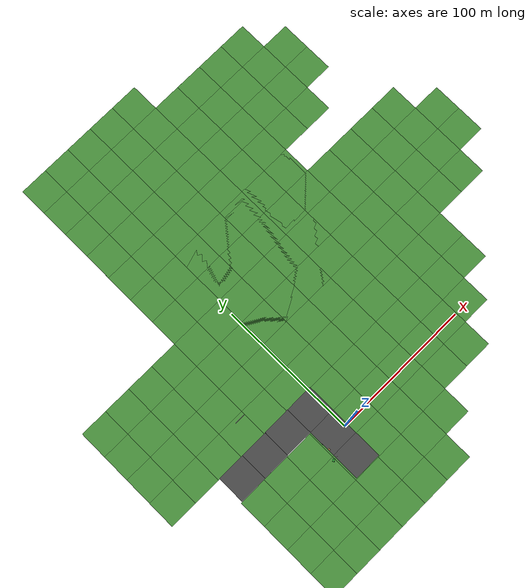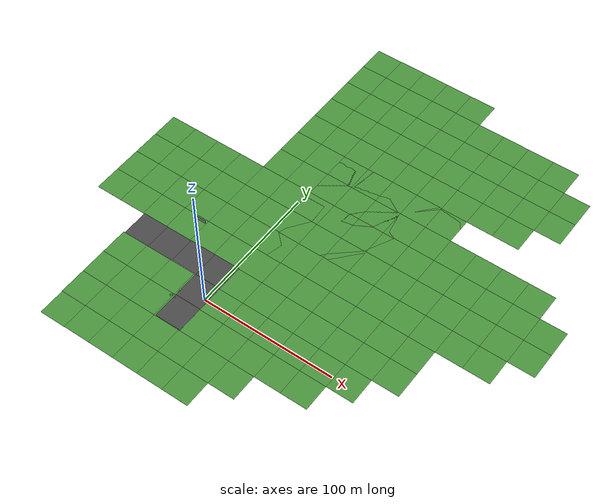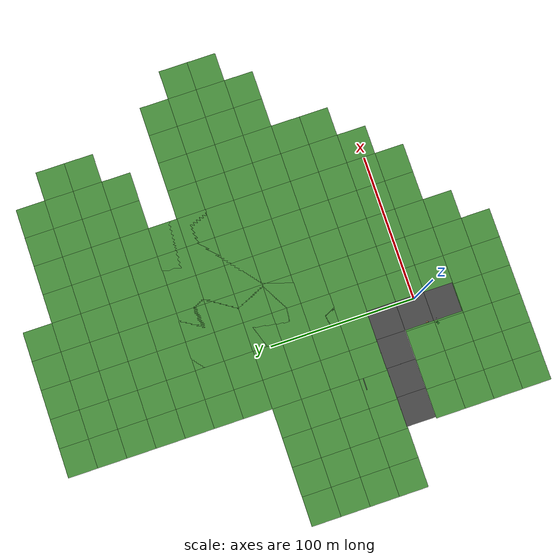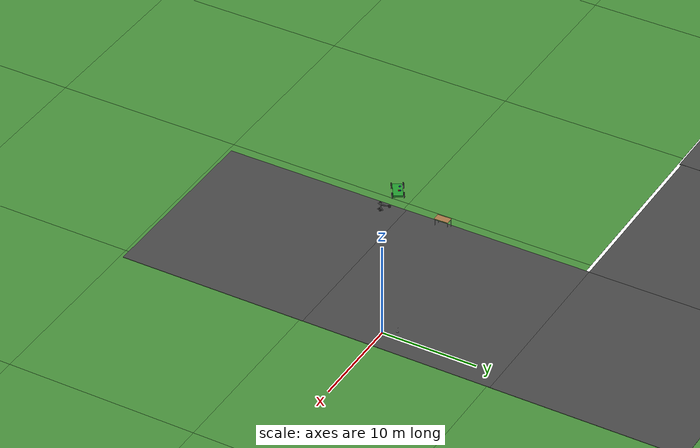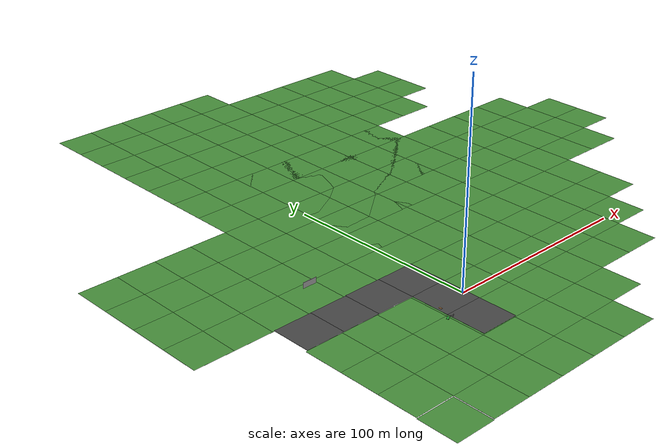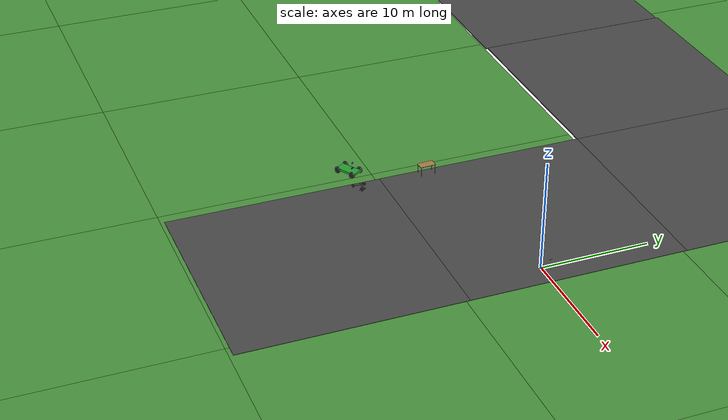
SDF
<sdf version="1.7">
 <world name="yolo_test_world">
  <light name="sun" type="directional">
   <pose>0 0 10 0 -0 0</pose>
   <diffuse>0.8 0.8 0.8 1</diffuse>
   <specular>0.2 0.2 0.2 1</specular>
   <attenuation>
    <range>1000</range>
    <constant>0.9</constant>
    <linear>0.01</linear>
    <quadratic>0.001</quadratic>
   </attenuation>
   <direction>-0.5 0.1 -0.9</direction>
   <spot><inner_angle>0</inner_angle><outer_angle>0</outer_angle><falloff>0</falloff></spot>
  </light>
  <gravity>0 0 -9.8</gravity>
  <magnetic_field>6e-06 2.3e-05 -4.2e-05</magnetic_field>
  <atmosphere type="adiabatic"/>
  <physics type="ode">
   <max_step_size>0.001</max_step_size>
   <real_time_factor>1</real_time_factor>
   <real_time_update_rate>1000</real_time_update_rate>
  </physics>
  <scene><ambient>0.4 0.4 0.4 1</ambient><background>0.7 0.7 0.7 1</background><shadows>1</shadows></scene>
  <audio><device>default</device></audio>
  <spherical_coordinates>
   <surface_model>EARTH_WGS84</surface_model>
   <latitude_deg>0</latitude_deg>
   <longitude_deg>0</longitude_deg>
   <elevation>0</elevation>
   <heading_deg>0</heading_deg>
  </spherical_coordinates>
  <model name="helios">
   <link name="base_link">
    <inertial>
     <pose>0 0 -0.025 0 -0 0</pose>
     <mass>1</mass>
     <inertia>
      <ixx>0.000333333</ixx>
      <ixy>0</ixy>
      <ixz>0</ixz>
      <iyy>0.000333333</iyy>
      <iyz>0</iyz>
      <izz>0.000333333</izz>
     </inertia>
    </inertial>
    <collision name="base_link_fixed_joint_lump__collision_chassis_collision">
     <geometry><box><size>0.2 0.1 0.05</size></box></geometry>
    </collision>
    <visual name="base_link_fixed_joint_lump__visual_chassis_visual">
     <geometry><box><size>0.2 0.1 0.05</size></box></geometry>
    </visual>
    <visual name="base_link_fixed_joint_lump__rgb_cam_camera_link_visual_1">
     <pose>0.04 0 0.5 0 -0 0</pose>
     <geometry><box><size>0.02 0.04 0.01</size></box></geometry>
    </visual>
    <sensor name="rgb_cam" type="camera">
     <always_on>1</always_on>
     <update_rate>10</update_rate>
     <camera name="rgb_cam">
      <horizontal_fov>1.39626</horizontal_fov>
      <image><width>640</width><height>480</height><format>R8G8B8</format></image>
      <clip><near>0.005</near><far>20</far></clip>
     </camera>
     <plugin name="camera_controller" filename="libgazebo_ros_camera.so">
      <alwaysOn>1</alwaysOn>
      <updateRate>0.0</updateRate>
      <cameraName>rgb_cam</cameraName>
      <imageTopicName>image_raw</imageTopicName>
      <cameraInfoTopicName>camera_info</cameraInfoTopicName>
      <frameName>rgb_cam_camera_link_frame</frameName>
      <hackBaseline>0.07</hackBaseline>
      <distortionK1>0.0</distortionK1>
      <distortionK2>0.0</distortionK2>
      <distortionK3>0.0</distortionK3>
      <distortionT1>0.0</distortionT1>
      <distortionT2>0.0</distortionT2>
     </plugin>
     <pose>0.05 0 0.5 0 -0 0</pose>
    </sensor>
   </link>
   <joint name="front_yaw_joint" type="revolute">
    <pose relative_to="base_link">0.08 0 -0.05 0 -0 0</pose>
    <parent>base_link</parent>
    <child>front_yaw_link</child>
    <axis>
     <xyz>0 0 1</xyz>
     <limit><effort>1000</effort><velocity>100</velocity><lower>-1e+16</lower><upper>1e+16</upper></limit>
     <dynamics>
      <damping>0</damping>
      <friction>0.1</friction>
      <spring_reference>0</spring_reference>
      <spring_stiffness>0</spring_stiffness>
     </dynamics>
    </axis>
   </joint>
   <link name="front_yaw_link">
    <pose relative_to="front_yaw_joint">0 0 0 0 -0 0</pose>
    <inertial>
     <pose>0 0 0 -0 1.5707 1.5707</pose>
     <mass>0.001</mass>
     <inertia>
      <ixx>5.14583e-09</ixx>
      <ixy>0</ixy>
      <ixz>0</ixz>
      <iyy>5.14583e-09</iyy>
      <iyz>0</iyz>
      <izz>1.0125e-08</izz>
     </inertia>
    </inertial>
    <collision name="front_yaw_link_fixed_joint_lump__link_right_wheel_collision_collision">
     <pose>0 0 0 1.57089 1.57079 -3.14159</pose>
     <geometry><cylinder><length>0.001</length><radius>0.0045</radius></cylinder></geometry>
    </collision>
   </link>
   <joint name="front_roll_joint" type="revolute">
    <pose relative_to="front_yaw_link">0 0 0 0 -0 0</pose>
    <parent>front_yaw_link</parent>
    <child>front_roll_link</child>
    <axis>
     <xyz>1 0 0</xyz>
     <limit><effort>1000</effort><velocity>100</velocity><lower>-1e+16</lower><upper>1e+16</upper></limit>
     <dynamics>
      <damping>0</damping>
      <friction>0.1</friction>
      <spring_reference>0</spring_reference>
      <spring_stiffness>0</spring_stiffness>
     </dynamics>
    </axis>
   </joint>
   <link name="front_roll_link">
    <pose relative_to="front_roll_joint">0 0 0 0 -0 0</pose>
    <inertial>
     <pose>0 0 0 -0 1.5707 1.5707</pose>
     <mass>0.001</mass>
     <inertia>
      <ixx>5.14583e-09</ixx>
      <ixy>0</ixy>
      <ixz>0</ixz>
      <iyy>5.14583e-09</iyy>
      <iyz>0</iyz>
      <izz>1.0125e-08</izz>
     </inertia>
    </inertial>
    <collision name="front_roll_link_fixed_joint_lump__link_right_wheel_collision_collision">
     <pose>0 0 0 1.57089 1.57079 -3.14159</pose>
     <geometry><cylinder><length>0.001</length><radius>0.0045</radius></cylinder></geometry>
    </collision>
   </link>
   <joint name="front_pitch_joint" type="revolute">
    <pose relative_to="front_roll_link">0 0 0 0 -0 0</pose>
    <parent>front_roll_link</parent>
    <child>front_pitch_link</child>
    <axis>
     <xyz>0 1 0</xyz>
     <limit><effort>1000</effort><velocity>100</velocity><lower>-1e+16</lower><upper>1e+16</upper></limit>
     <dynamics>
      <damping>0</damping>
      <friction>0.1</friction>
      <spring_reference>0</spring_reference>
      <spring_stiffness>0</spring_stiffness>
     </dynamics>
    </axis>
   </joint>
   <link name="front_pitch_link">
    <pose relative_to="front_pitch_joint">0 0 0 0 -0 0</pose>
    <inertial>
     <pose>0 0 0 -0 1.5707 1.5707</pose>
     <mass>0.001</mass>
     <inertia><ixx>4e-08</ixx><ixy>0</ixy><ixz>0</ixz><iyy>4e-08</iyy><iyz>0</iyz><izz>4e-08</izz></inertia>
    </inertial>
    <collision name="front_pitch_link_fixed_joint_lump__front_collision_collision">
     <pose>0 0 0 1.57089 1.57079 -3.14159</pose>
     <geometry><sphere><radius>0.01</radius></sphere></geometry>
    </collision>
    <visual name="front_pitch_link_fixed_joint_lump__front_visual_visual">
     <pose>0 0 0 1.57089 1.57079 -3.14159</pose>
     <geometry><sphere><radius>0.01</radius></sphere></geometry>
    </visual>
   </link>
   <joint name="joint_left_wheel" type="revolute">
    <pose relative_to="base_link">-0.05 -0.05 -0.025 0 -0 0</pose>
    <parent>base_link</parent>
    <child>left_wheel</child>
    <axis>
     <xyz>0 1 0</xyz>
     <limit><effort>10000</effort><velocity>1000</velocity><lower>-1e+16</lower><upper>1e+16</upper></limit>
     <dynamics><spring_reference>0</spring_reference><spring_stiffness>0</spring_stiffness></dynamics>
    </axis>
   </joint>
   <link name="left_wheel">
    <pose relative_to="joint_left_wheel">0 0 0 0 -0 0</pose>
    <inertial>
     <pose>0 0 0 -0 1.5707 1.5707</pose>
     <mass>0.2</mass>
     <inertia>
      <ixx>3.12667e-05</ixx>
      <ixy>0</ixy>
      <ixz>0</ixz>
      <iyy>3.12667e-05</iyy>
      <iyz>0</iyz>
      <izz>6.25e-05</izz>
     </inertia>
    </inertial>
    <collision name="left_wheel_fixed_joint_lump__link_right_wheel_collision_collision">
     <pose>0 0 0 1.57089 1.57079 -3.14159</pose>
     <geometry><cylinder><length>0.01</length><radius>0.035</radius></cylinder></geometry>
    </collision>
    <visual name="left_wheel_fixed_joint_lump__link_right_wheel_visual_visual">
     <pose>0 0 0 1.57089 1.57079 -3.14159</pose>
     <geometry><cylinder><length>0.01</length><radius>0.035</radius></cylinder></geometry>
    </visual>
   </link>
   <joint name="joint_right_wheel" type="revolute">
    <pose relative_to="base_link">-0.05 0.05 -0.025 0 -0 0</pose>
    <parent>base_link</parent>
    <child>right_wheel</child>
    <axis>
     <xyz>0 1 0</xyz>
     <limit><effort>10000</effort><velocity>1000</velocity><lower>-1e+16</lower><upper>1e+16</upper></limit>
     <dynamics><spring_reference>0</spring_reference><spring_stiffness>0</spring_stiffness></dynamics>
    </axis>
   </joint>
   <link name="right_wheel">
    <pose relative_to="joint_right_wheel">0 0 0 0 -0 0</pose>
    <inertial>
     <pose>0 0 0 -0 1.5707 1.5707</pose>
     <mass>0.2</mass>
     <inertia>
      <ixx>3.12667e-05</ixx>
      <ixy>0</ixy>
      <ixz>0</ixz>
      <iyy>3.12667e-05</iyy>
      <iyz>0</iyz>
      <izz>6.25e-05</izz>
     </inertia>
    </inertial>
    <collision name="right_wheel_fixed_joint_lump__link_right_wheel_collision_collision">
     <pose>0 0 0 1.57089 1.57079 -3.14159</pose>
     <geometry><cylinder><length>0.01</length><radius>0.035</radius></cylinder></geometry>
    </collision>
    <visual name="right_wheel_fixed_joint_lump__link_right_wheel_visual_visual">
     <pose>0 0 0 1.57089 1.57079 -3.14159</pose>
     <geometry><cylinder><length>0.01</length><radius>0.035</radius></cylinder></geometry>
    </visual>
   </link>
   <plugin name="gazebo_ros_control" filename="libgazebo_ros_control.so">
    <robotNamespace>/helios</robotNamespace>
    <robotParam>/robot_description</robotParam>
    <robotSimType>gazebo_ros_control/DefaultRobotHWSim</robotSimType>
   </plugin>
   <plugin name="differential_drive_controller" filename="libgazebo_ros_diff_drive.so">
    <ros><namespace>/helios</namespace></ros>
    <left_joint>joint_right_wheel</left_joint>
    <right_joint>joint_left_wheel</right_joint>
    <wheel_separation>0.1</wheel_separation>
    <wheel_diameter>0.025</wheel_diameter>
    <max_wheel_torque>0.1</max_wheel_torque>
    <max_wheel_acceleration>1.0</max_wheel_acceleration>
    <publish_odom>1</publish_odom>
    <publish_odom_tf>1</publish_odom_tf>
    <odometry_frame>odom</odometry_frame>
    <robot_base_frame>chassis</robot_base_frame>
   </plugin>
   <static>0</static>
   <plugin name="gazebo_ros_imu_controller" filename="libgazebo_ros_imu.so">
    <robotNamespace>/helios/</robotNamespace>
    <topicName>imu/data3</topicName>
    <serviceName>imu/service</serviceName>
    <gaussianNoise>0</gaussianNoise>
    <rpyOffsets>0 0 0</rpyOffsets>
    <updateRate>50.0</updateRate>
    <alwaysOn>1</alwaysOn>
    <gaussianNoise>0</gaussianNoise>
    <bodyName>base_link</bodyName>
    <xyzOffset>0 0 0</xyzOffset>
    <rpyOffset>0 -0 0</rpyOffset>
   </plugin>
   <pose>-0.710325 1.23366 0.109516 1.6e-05 0.009595 1.63934</pose>
  </model>
  <model name="table">
   <static>1</static>
   <link name="link">
    <collision name="surface">
     <pose>0 0 1 0 -0 0</pose>
     <geometry><box><size>1.5 0.8 0.03</size></box></geometry>
     <surface><friction><ode><mu>0.6</mu><mu2>0.6</mu2></ode></friction></surface>
    </collision>
    <visual name="visual1">
     <pose>0 0 1 0 -0 0</pose>
     <geometry><box><size>1.5 0.8 0.03</size></box></geometry>
     <material>
      <script><uri>file://media/materials/scripts/gazebo.material</uri><name>Gazebo/Wood</name></script>
     </material>
    </visual>
    <collision name="front_left_leg">
     <pose>0.68 0.38 0.5 0 -0 0</pose>
     <geometry><cylinder><radius>0.02</radius><length>1</length></cylinder></geometry>
    </collision>
    <visual name="front_left_leg">
     <pose>0.68 0.38 0.5 0 -0 0</pose>
     <geometry><cylinder><radius>0.02</radius><length>1</length></cylinder></geometry>
     <material>
      <script><uri>file://media/materials/scripts/gazebo.material</uri><name>Gazebo/Grey</name></script>
     </material>
    </visual>
    <collision name="front_right_leg">
     <pose>0.68 -0.38 0.5 0 -0 0</pose>
     <geometry><cylinder><radius>0.02</radius><length>1</length></cylinder></geometry>
    </collision>
    <visual name="front_right_leg">
     <pose>0.68 -0.38 0.5 0 -0 0</pose>
     <geometry><cylinder><radius>0.02</radius><length>1</length></cylinder></geometry>
     <material>
      <script><uri>file://media/materials/scripts/gazebo.material</uri><name>Gazebo/Grey</name></script>
     </material>
    </visual>
    <collision name="back_right_leg">
     <pose>-0.68 -0.38 0.5 0 -0 0</pose>
     <geometry><cylinder><radius>0.02</radius><length>1</length></cylinder></geometry>
    </collision>
    <visual name="back_right_leg">
     <pose>-0.68 -0.38 0.5 0 -0 0</pose>
     <geometry><cylinder><radius>0.02</radius><length>1</length></cylinder></geometry>
     <material>
      <script><uri>file://media/materials/scripts/gazebo.material</uri><name>Gazebo/Grey</name></script>
     </material>
    </visual>
    <collision name="back_left_leg">
     <pose>-0.68 0.38 0.5 0 -0 0</pose>
     <geometry><cylinder><radius>0.02</radius><length>1</length></cylinder></geometry>
    </collision>
    <visual name="back_left_leg">
     <pose>-0.68 0.38 0.5 0 -0 0</pose>
     <geometry><cylinder><radius>0.02</radius><length>1</length></cylinder></geometry>
     <material>
      <script><uri>file://media/materials/scripts/gazebo.material</uri><name>Gazebo/Grey</name></script>
     </material>
    </visual>
   </link>
   <pose>-17.2099 -3.0253 0 0 -0 1.59866</pose>
  </model>
  <model name="trisphere_cycle">
   <link name="frame">
    <pose>-0.408559 0 0.385023 0 -0.522021 0</pose>
    <inertial>
     <mass>10</mass>
     <inertia><ixx>0.228</ixx><iyy>0.743521</iyy><izz>0.965521</izz><ixy>0</ixy><ixz>0</ixz><iyz>0</iyz></inertia>
    </inertial>
    <collision name="axle_collision">
     <pose>-0.471335 0 0 1.5708 -0 0</pose>
     <geometry><cylinder><length>1.03923</length><radius>0.03</radius></cylinder></geometry>
    </collision>
    <visual name="axle_visual">
     <pose>-0.471335 0 0 1.5708 -0 0</pose>
     <geometry><cylinder><length>1.03923</length><radius>0.03</radius></cylinder></geometry>
     <material>
      <script><uri>file://media/materials/scripts/gazebo.material</uri><name>Gazebo/Grey</name></script>
     </material>
    </visual>
    <collision name="frame_left_collision">
     <pose>0 0.171552 0 -2.79253 1.57079 3.14159</pose>
     <geometry><cylinder><length>1.00317</length><radius>0.03</radius></cylinder></geometry>
    </collision>
    <visual name="frame_left_visual">
     <pose>0 0.171552 0 -2.79253 1.57079 3.14159</pose>
     <geometry><cylinder><length>1.00317</length><radius>0.03</radius></cylinder></geometry>
     <material>
      <script><uri>file://media/materials/scripts/gazebo.material</uri><name>Gazebo/Grey</name></script>
     </material>
    </visual>
    <collision name="frame_right_collision">
     <pose>0 -0.171552 0 2.79253 1.57079 -3.14159</pose>
     <geometry><cylinder><length>1.00317</length><radius>0.03</radius></cylinder></geometry>
    </collision>
    <visual name="frame_right_visual">
     <pose>0 -0.171552 0 2.79253 1.57079 -3.14159</pose>
     <geometry><cylinder><length>1.00317</length><radius>0.03</radius></cylinder></geometry>
     <material>
      <script><uri>file://media/materials/scripts/gazebo.material</uri><name>Gazebo/Grey</name></script>
     </material>
    </visual>
   </link>
   <link name="fork">
    <pose>0.041441 0 0.385023 0 -0.174533 0</pose>
    <inertial>
     <mass>3</mass>
     <inertia>
      <ixx>0.158203</ixx>
      <iyy>0.0583594</iyy>
      <izz>0.102656</izz>
      <ixy>0</ixy>
      <ixz>0</ixz>
      <iyz>0</iyz>
     </inertia>
    </inertial>
    <collision name="handlebars_collision">
     <pose>0 0 0.397748 1.5708 -0 0</pose>
     <geometry><cylinder><length>0.636396</length><radius>0.0375</radius></cylinder></geometry>
    </collision>
    <visual name="handlebars_visual">
     <pose>0 0 0.397748 1.5708 -0 0</pose>
     <geometry><cylinder><length>0.636396</length><radius>0.0375</radius></cylinder></geometry>
     <material>
      <script><uri>file://media/materials/scripts/gazebo.material</uri><name>Gazebo/Grey</name></script>
     </material>
    </visual>
    <collision name="headtube_collision">
     <pose>0 0 0.238649 0 -0 0</pose>
     <geometry><cylinder><length>0.318198</length><radius>0.0375</radius></cylinder></geometry>
    </collision>
    <visual name="headtube_visual">
     <pose>0 0 0.238649 0 -0 0</pose>
     <geometry><cylinder><length>0.318198</length><radius>0.0375</radius></cylinder></geometry>
     <material>
      <script><uri>file://media/materials/scripts/gazebo.material</uri><name>Gazebo/Grey</name></script>
     </material>
    </visual>
    <collision name="spindle_collision">
     <pose>0 0 -0.238649 1.5708 -0 0</pose>
     <geometry><cylinder><length>0.636396</length><radius>0.015</radius></cylinder></geometry>
    </collision>
    <visual name="spindle_visual">
     <pose>0 0 -0.238649 1.5708 -0 0</pose>
     <geometry><cylinder><length>0.636396</length><radius>0.015</radius></cylinder></geometry>
     <material>
      <script><uri>file://media/materials/scripts/gazebo.material</uri><name>Gazebo/Grey</name></script>
     </material>
    </visual>
    <collision name="fork_left_collision">
     <pose>0 0.159099 -0.07955 0.785398 -0 0</pose>
     <geometry><cylinder><length>0.45</length><radius>0.0375</radius></cylinder></geometry>
    </collision>
    <visual name="fork_left_visual">
     <pose>0 0.159099 -0.07955 0.785398 -0 0</pose>
     <geometry><cylinder><length>0.45</length><radius>0.0375</radius></cylinder></geometry>
     <material>
      <script><uri>file://media/materials/scripts/gazebo.material</uri><name>Gazebo/Grey</name></script>
     </material>
    </visual>
    <collision name="fork_right_collision">
     <pose>0 -0.159099 -0.07955 -0.785398 0 0</pose>
     <geometry><cylinder><length>0.45</length><radius>0.0375</radius></cylinder></geometry>
    </collision>
    <visual name="fork_right_visual">
     <pose>0 -0.159099 -0.07955 -0.785398 0 0</pose>
     <geometry><cylinder><length>0.45</length><radius>0.0375</radius></cylinder></geometry>
     <material>
      <script><uri>file://media/materials/scripts/gazebo.material</uri><name>Gazebo/Grey</name></script>
     </material>
    </visual>
   </link>
   <link name="wheel_front">
    <pose>0.082882 0 0.15 0 -0 0</pose>
    <inertial>
     <mass>0.5</mass>
     <inertia><ixx>0.0045</ixx><iyy>0.0045</iyy><izz>0.0045</izz><ixy>0</ixy><ixz>0</ixz><iyz>0</iyz></inertia>
    </inertial>
    <collision name="collision">
     <geometry><sphere><radius>0.15</radius></sphere></geometry>
     <surface><contact><ode><kp>1e+08</kp><kd>1</kd><min_depth>0.0005</min_depth></ode></contact></surface>
    </collision>
    <visual name="visual">
     <geometry><sphere><radius>0.15</radius></sphere></geometry>
     <material>
      <script><uri>file://media/materials/scripts/gazebo.material</uri><name>Gazebo/Black</name></script>
     </material>
    </visual>
   </link>
   <joint name="wheel_front_steer" type="revolute">
    <parent>frame</parent>
    <child>fork</child>
    <axis>
     <xyz>0 0 1</xyz>
     <limit><lower>-0.959931</lower><upper>0.959931</upper></limit>
     <dynamics><spring_reference>0</spring_reference><spring_stiffness>0</spring_stiffness></dynamics>
    </axis>
   </joint>
   <joint name="wheel_front_spin" type="revolute">
    <parent>fork</parent>
    <child>wheel_front</child>
    <axis>
     <xyz>0 1 0</xyz>
     <limit><lower>-1e+16</lower><upper>1e+16</upper></limit>
     <dynamics><spring_reference>0</spring_reference><spring_stiffness>0</spring_stiffness></dynamics>
    </axis>
   </joint>
   <link name="wheel_rear_left">
    <pose>-0.817118 0.519615 0.15 0 -0 0</pose>
    <inertial>
     <mass>0.5</mass>
     <inertia><ixx>0.0045</ixx><iyy>0.0045</iyy><izz>0.0045</izz><ixy>0</ixy><ixz>0</ixz><iyz>0</iyz></inertia>
    </inertial>
    <collision name="collision">
     <geometry><sphere><radius>0.15</radius></sphere></geometry>
     <surface><contact><ode><kp>1e+08</kp><kd>1</kd><min_depth>0.0005</min_depth></ode></contact></surface>
    </collision>
    <visual name="visual">
     <geometry><sphere><radius>0.15</radius></sphere></geometry>
     <material>
      <script><uri>file://media/materials/scripts/gazebo.material</uri><name>Gazebo/Black</name></script>
     </material>
    </visual>
   </link>
   <joint name="wheel_rear_left_spin" type="revolute">
    <parent>frame</parent>
    <child>wheel_rear_left</child>
    <axis>
     <xyz>0 1 0</xyz>
     <limit><lower>-1e+16</lower><upper>1e+16</upper></limit>
     <dynamics><spring_reference>0</spring_reference><spring_stiffness>0</spring_stiffness></dynamics>
    </axis>
   </joint>
   <link name="wheel_rear_right">
    <pose>-0.817118 -0.519615 0.15 0 -0 0</pose>
    <inertial>
     <mass>0.5</mass>
     <inertia><ixx>0.0045</ixx><iyy>0.0045</iyy><izz>0.0045</izz><ixy>0</ixy><ixz>0</ixz><iyz>0</iyz></inertia>
    </inertial>
    <collision name="collision">
     <geometry><sphere><radius>0.15</radius></sphere></geometry>
     <surface><contact><ode><kp>1e+08</kp><kd>1</kd><min_depth>0.0005</min_depth></ode></contact></surface>
    </collision>
    <visual name="visual">
     <geometry><sphere><radius>0.15</radius></sphere></geometry>
     <material>
      <script><uri>file://media/materials/scripts/gazebo.material</uri><name>Gazebo/Black</name></script>
     </material>
    </visual>
   </link>
   <joint name="wheel_rear_right_spin" type="revolute">
    <parent>frame</parent>
    <child>wheel_rear_right</child>
    <axis>
     <xyz>0 1 0</xyz>
     <limit><lower>-1e+16</lower><upper>1e+16</upper></limit>
     <dynamics><spring_reference>0</spring_reference><spring_stiffness>0</spring_stiffness></dynamics>
    </axis>
   </joint>
   <pose>-16.5218 -9.55628 0.049499 0 1e-06 -0.004009</pose>
  </model>
  <model name="car">
   <link name="chassis">
    <pose>0 0 0.3 0 -0 0</pose>
    <collision name="collision"><geometry><box><size>2 1 0.2</size></box></geometry></collision>
    <visual name="visual">
     <geometry><box><size>2 1 0.2</size></box></geometry>
     <material>
      <script><uri>file://media/materials/scripts/gazebo.material</uri><name>Gazebo/Green</name></script>
     </material>
    </visual>
    <inertial>
     <inertia><ixx>1</ixx><ixy>0</ixy><ixz>0</ixz><iyy>1</iyy><iyz>0</iyz><izz>1</izz></inertia>
     <mass>1</mass>
    </inertial>
   </link>
   <link name="front_left_wheel">
    <pose>0.8 0.6 0.3 -0 1.5707 1.5707</pose>
    <collision name="collision">
     <geometry><cylinder><radius>0.3</radius><length>0.1</length></cylinder></geometry>
    </collision>
    <visual name="visual">
     <geometry><cylinder><radius>0.3</radius><length>0.1</length></cylinder></geometry>
     <material>
      <script><uri>file://media/materials/scripts/gazebo.material</uri><name>Gazebo/Black</name></script>
     </material>
    </visual>
    <inertial>
     <inertia><ixx>1</ixx><ixy>0</ixy><ixz>0</ixz><iyy>1</iyy><iyz>0</iyz><izz>1</izz></inertia>
     <mass>1</mass>
    </inertial>
   </link>
   <link name="front_right_wheel">
    <pose>0.8 -0.6 0.3 -0 1.5707 1.5707</pose>
    <collision name="collision">
     <geometry><cylinder><radius>0.3</radius><length>0.1</length></cylinder></geometry>
    </collision>
    <visual name="visual">
     <geometry><cylinder><radius>0.3</radius><length>0.1</length></cylinder></geometry>
     <material>
      <script><uri>file://media/materials/scripts/gazebo.material</uri><name>Gazebo/Black</name></script>
     </material>
    </visual>
    <inertial>
     <inertia><ixx>1</ixx><ixy>0</ixy><ixz>0</ixz><iyy>1</iyy><iyz>0</iyz><izz>1</izz></inertia>
     <mass>1</mass>
    </inertial>
   </link>
   <link name="back_right_wheel">
    <pose>-0.8 -0.6 0.3 -0 1.5707 1.5707</pose>
    <collision name="collision">
     <geometry><cylinder><radius>0.3</radius><length>0.1</length></cylinder></geometry>
    </collision>
    <visual name="visual">
     <geometry><cylinder><radius>0.3</radius><length>0.1</length></cylinder></geometry>
     <material>
      <script><uri>file://media/materials/scripts/gazebo.material</uri><name>Gazebo/Black</name></script>
     </material>
    </visual>
    <inertial>
     <inertia><ixx>1</ixx><ixy>0</ixy><ixz>0</ixz><iyy>1</iyy><iyz>0</iyz><izz>1</izz></inertia>
     <mass>1</mass>
    </inertial>
   </link>
   <link name="back_left_wheel">
    <pose>-0.8 0.6 0.3 -0 1.5707 1.5707</pose>
    <collision name="collision">
     <geometry><cylinder><radius>0.3</radius><length>0.1</length></cylinder></geometry>
    </collision>
    <visual name="visual">
     <geometry><cylinder><radius>0.3</radius><length>0.1</length></cylinder></geometry>
     <material>
      <script><uri>file://media/materials/scripts/gazebo.material</uri><name>Gazebo/Black</name></script>
     </material>
    </visual>
    <inertial>
     <inertia><ixx>1</ixx><ixy>0</ixy><ixz>0</ixz><iyy>1</iyy><iyz>0</iyz><izz>1</izz></inertia>
     <mass>1</mass>
    </inertial>
   </link>
   <link name="gas_pedal">
    <pose>0.3 0.1 0.5 0 -0 0</pose>
    <collision name="collision"><geometry><box><size>0.1 0.1 0.1</size></box></geometry></collision>
    <visual name="visual">
     <geometry><box><size>0.1 0.1 0.1</size></box></geometry>
     <material>
      <script><uri>file://media/materials/scripts/gazebo.material</uri><name>Gazebo/Red</name></script>
     </material>
    </visual>
    <inertial>
     <inertia><ixx>1</ixx><ixy>0</ixy><ixz>0</ixz><iyy>1</iyy><iyz>0</iyz><izz>1</izz></inertia>
     <mass>1</mass>
    </inertial>
   </link>
   <link name="brake_pedal">
    <pose>0.3 0.25 0.5 0 -0 0</pose>
    <collision name="collision"><geometry><box><size>0.1 0.1 0.1</size></box></geometry></collision>
    <visual name="visual">
     <geometry><box><size>0.1 0.1 0.1</size></box></geometry>
     <material>
      <script><uri>file://media/materials/scripts/gazebo.material</uri><name>Gazebo/Blue</name></script>
     </material>
    </visual>
    <inertial>
     <inertia><ixx>1</ixx><ixy>0</ixy><ixz>0</ixz><iyy>1</iyy><iyz>0</iyz><izz>1</izz></inertia>
     <mass>1</mass>
    </inertial>
   </link>
   <link name="steering_wheel">
    <pose>0.3 0.2 1 0 1.5707 0</pose>
    <collision name="collision">
     <geometry><cylinder><radius>0.1</radius><length>0.01</length></cylinder></geometry>
    </collision>
    <visual name="visual">
     <geometry><cylinder><radius>0.1</radius><length>0.01</length></cylinder></geometry>
     <material>
      <script><uri>file://media/materials/scripts/gazebo.material</uri><name>Gazebo/Blue</name></script>
     </material>
    </visual>
    <inertial>
     <inertia><ixx>1</ixx><ixy>0</ixy><ixz>0</ixz><iyy>1</iyy><iyz>0</iyz><izz>1</izz></inertia>
     <mass>1</mass>
    </inertial>
   </link>
   <joint name="gas_joint" type="prismatic">
    <parent>chassis</parent>
    <child>gas_pedal</child>
    <axis>
     <xyz expressed_in="__model__">1 0 0</xyz>
     <limit><lower>0</lower><upper>0.2</upper></limit>
     <dynamics><spring_reference>0</spring_reference><spring_stiffness>0</spring_stiffness></dynamics>
    </axis>
   </joint>
   <joint name="brake_joint" type="prismatic">
    <parent>chassis</parent>
    <child>brake_pedal</child>
    <axis>
     <xyz expressed_in="__model__">1 0 0</xyz>
     <limit><lower>0</lower><upper>0.2</upper></limit>
     <dynamics><spring_reference>0</spring_reference><spring_stiffness>0</spring_stiffness></dynamics>
    </axis>
   </joint>
   <joint name="steering_joint" type="revolute">
    <parent>chassis</parent>
    <child>steering_wheel</child>
    <axis>
     <xyz expressed_in="__model__">1 0 0</xyz>
     <limit><lower>-7.853</lower><upper>7.853</upper></limit>
     <dynamics><spring_reference>0</spring_reference><spring_stiffness>0</spring_stiffness></dynamics>
    </axis>
   </joint>
   <joint name="front_left_joint" type="revolute2">
    <parent>chassis</parent>
    <child>front_left_wheel</child>
    <axis>
     <xyz expressed_in="__model__">0 0 1</xyz>
     <limit><lower>2.40026e-07</lower><upper>2.40026e-07</upper></limit>
     <dynamics><spring_reference>0</spring_reference><spring_stiffness>0</spring_stiffness></dynamics>
    </axis>
    <axis2>
     <xyz expressed_in="__model__">0 1 0</xyz>
     <limit><upper>1e+16</upper><lower>-1e+16</lower></limit>
     <dynamics><spring_reference>0</spring_reference><spring_stiffness>0</spring_stiffness></dynamics>
    </axis2>
    <physics><ode><limit><cfm>0</cfm><erp>0.9</erp></limit></ode></physics>
   </joint>
   <joint name="front_right_joint" type="revolute2">
    <parent>chassis</parent>
    <child>front_right_wheel</child>
    <axis>
     <xyz expressed_in="__model__">0 0 1</xyz>
     <limit><lower>2.40026e-07</lower><upper>2.40026e-07</upper></limit>
     <dynamics><spring_reference>0</spring_reference><spring_stiffness>0</spring_stiffness></dynamics>
    </axis>
    <axis2>
     <xyz expressed_in="__model__">0 1 0</xyz>
     <limit><upper>1e+16</upper><lower>-1e+16</lower></limit>
     <dynamics><spring_reference>0</spring_reference><spring_stiffness>0</spring_stiffness></dynamics>
    </axis2>
    <physics><ode><limit><cfm>0</cfm><erp>0.9</erp></limit></ode></physics>
   </joint>
   <joint name="back_right_joint" type="revolute2">
    <parent>chassis</parent>
    <child>back_right_wheel</child>
    <axis>
     <xyz expressed_in="__model__">0 0 1</xyz>
     <limit><lower>0</lower><upper>0</upper></limit>
     <dynamics><spring_reference>0</spring_reference><spring_stiffness>0</spring_stiffness></dynamics>
    </axis>
    <axis2>
     <xyz expressed_in="__model__">0 1 0</xyz>
     <limit><upper>1e+16</upper><lower>-1e+16</lower></limit>
     <dynamics><spring_reference>0</spring_reference><spring_stiffness>0</spring_stiffness></dynamics>
    </axis2>
    <physics><ode><limit><cfm>0</cfm><erp>0.9</erp></limit></ode></physics>
   </joint>
   <joint name="back_left_joint" type="revolute2">
    <parent>chassis</parent>
    <child>back_left_wheel</child>
    <axis>
     <xyz expressed_in="__model__">0 0 1</xyz>
     <limit><lower>0</lower><upper>0</upper></limit>
     <dynamics><spring_reference>0</spring_reference><spring_stiffness>0</spring_stiffness></dynamics>
    </axis>
    <axis2>
     <xyz expressed_in="__model__">0 1 0</xyz>
     <limit><upper>1e+16</upper><lower>-1e+16</lower></limit>
     <dynamics><spring_reference>0</spring_reference><spring_stiffness>0</spring_stiffness></dynamics>
    </axis2>
    <physics><ode><limit><cfm>0</cfm><erp>0.9</erp></limit></ode></physics>
   </joint>
   <plugin name="vehicle" filename="libVehiclePlugin.so">
    <front_left>front_left_joint</front_left>
    <front_right>front_right_joint</front_right>
    <back_left>back_left_joint</back_left>
    <back_right>back_right_joint</back_right>
    <gas>gas_joint</gas>
    <brake>brake_joint</brake>
    <steering>steering_joint</steering>
    <front_power>10</front_power>
    <rear_power>10</rear_power>
    <tire_angle_range>0.5</tire_angle_range>
    <max_speed>10</max_speed>
    <aero_load>0.1</aero_load>
   </plugin>
   <pose>-19.906 -9.55458 8e-06 -2e-06 6e-06 0.564851</pose>
  </model>
  <model name="grey_wall">
   <static>1</static>
   <link name="link">
    <pose>0 0 1.4 0 -0 0</pose>
    <collision name="collision"><geometry><box><size>7.5 0.2 2.8</size></box></geometry></collision>
    <visual name="visual">
     <cast_shadows>0</cast_shadows>
     <geometry><box><size>7.5 0.2 2.8</size></box></geometry>
     <material>
      <script>
       <uri>model://grey_wall/materials/scripts</uri>
       <uri>model://grey_wall/materials/textures</uri>
       <name>vrc/grey_wall</name>
      </script>
     </material>
    </visual>
   </link>
   <pose>-43.0369 49.3353 0 0 -0 0</pose>
  </model>
  <model name="asphalt_plane">
   <static>1</static>
   <link name="link">
    <collision name="collision"><geometry><box><size>20 20 0.1</size></box></geometry></collision>
    <visual name="visual">
     <cast_shadows>0</cast_shadows>
     <geometry><box><size>20 20 0.1</size></box></geometry>
     <material>
      <script>
       <uri>model://asphalt_plane/materials/scripts</uri>
       <uri>model://asphalt_plane/materials/textures</uri>
       <name>vrc/asphalt</name>
      </script>
     </material>
    </visual>
   </link>
   <pose>-7.83882 2.61958 0 0 -0 0</pose>
  </model>
  <model name="asphalt_plane_0">
   <static>1</static>
   <link name="link">
    <collision name="collision"><geometry><box><size>20 20 0.1</size></box></geometry></collision>
    <visual name="visual">
     <cast_shadows>0</cast_shadows>
     <geometry><box><size>20 20 0.1</size></box></geometry>
     <material>
      <script>
       <uri>model://asphalt_plane/materials/scripts</uri>
       <uri>model://asphalt_plane/materials/textures</uri>
       <name>vrc/asphalt</name>
      </script>
     </material>
    </visual>
   </link>
   <pose>-7.82965 22.6179 0 0 -0 0</pose>
  </model>
  <model name="asphalt_plane_1">
   <static>1</static>
   <link name="link">
    <collision name="collision"><geometry><box><size>20 20 0.1</size></box></geometry></collision>
    <visual name="visual">
     <cast_shadows>0</cast_shadows>
     <geometry><box><size>20 20 0.1</size></box></geometry>
     <material>
      <script>
       <uri>model://asphalt_plane/materials/scripts</uri>
       <uri>model://asphalt_plane/materials/textures</uri>
       <name>vrc/asphalt</name>
      </script>
     </material>
    </visual>
   </link>
   <pose>-7.82531 -17.3703 0 0 -0 0</pose>
  </model>
  <model name="grass_plane">
   <static>1</static>
   <link name="link">
    <collision name="collision">
     <geometry><plane><normal>0 0 1</normal><size>500 500</size></plane></geometry>
     <surface><friction><ode><mu>0.5</mu><mu2>0.5</mu2></ode></friction></surface>
    </collision>
    <visual name="visual_0">
     <pose>-40 -40 0 0 -0 0</pose>
     <cast_shadows>0</cast_shadows>
     <geometry><plane><normal>0 0 1</normal><size>20 20</size></plane></geometry>
     <material>
      <script>
       <uri>https://fuel.ignitionrobotics.org/1.0/openrobotics/models/grass plane/2/files/materials/scripts</uri>
       <uri>https://fuel.ignitionrobotics.org/1.0/openrobotics/models/grass plane/2/files/materials/textures</uri>
       <name>vrc/grass</name>
      </script>
     </material>
    </visual>
    <visual name="visual_1">
     <pose>-20 -40 0 0 -0 0</pose>
     <cast_shadows>0</cast_shadows>
     <geometry><plane><normal>0 0 1</normal><size>20 20</size></plane></geometry>
     <material>
      <script>
       <uri>https://fuel.ignitionrobotics.org/1.0/openrobotics/models/grass plane/2/files/materials/scripts</uri>
       <uri>https://fuel.ignitionrobotics.org/1.0/openrobotics/models/grass plane/2/files/materials/textures</uri>
       <name>vrc/grass</name>
      </script>
     </material>
    </visual>
    <visual name="visual_2">
     <pose>0 -40 0 0 -0 0</pose>
     <cast_shadows>0</cast_shadows>
     <geometry><plane><normal>0 0 1</normal><size>20 20</size></plane></geometry>
     <material>
      <script>
       <uri>https://fuel.ignitionrobotics.org/1.0/openrobotics/models/grass plane/2/files/materials/scripts</uri>
       <uri>https://fuel.ignitionrobotics.org/1.0/openrobotics/models/grass plane/2/files/materials/textures</uri>
       <name>vrc/grass</name>
      </script>
     </material>
    </visual>
    <visual name="visual_3">
     <pose>20 -40 0 0 -0 0</pose>
     <cast_shadows>0</cast_shadows>
     <geometry><plane><normal>0 0 1</normal><size>20 20</size></plane></geometry>
     <material>
      <script>
       <uri>https://fuel.ignitionrobotics.org/1.0/openrobotics/models/grass plane/2/files/materials/scripts</uri>
       <uri>https://fuel.ignitionrobotics.org/1.0/openrobotics/models/grass plane/2/files/materials/textures</uri>
       <name>vrc/grass</name>
      </script>
     </material>
    </visual>
    <visual name="visual_4">
     <pose>40 -40 0 0 -0 0</pose>
     <cast_shadows>0</cast_shadows>
     <geometry><plane><normal>0 0 1</normal><size>20 20</size></plane></geometry>
     <material>
      <script>
       <uri>https://fuel.ignitionrobotics.org/1.0/openrobotics/models/grass plane/2/files/materials/scripts</uri>
       <uri>https://fuel.ignitionrobotics.org/1.0/openrobotics/models/grass plane/2/files/materials/textures</uri>
       <name>vrc/grass</name>
      </script>
     </material>
    </visual>
    <visual name="visual_5">
     <pose>60 -40 0 0 -0 0</pose>
     <cast_shadows>0</cast_shadows>
     <geometry><plane><normal>0 0 1</normal><size>20 20</size></plane></geometry>
     <material>
      <script>
       <uri>https://fuel.ignitionrobotics.org/1.0/openrobotics/models/grass plane/2/files/materials/scripts</uri>
       <uri>https://fuel.ignitionrobotics.org/1.0/openrobotics/models/grass plane/2/files/materials/textures</uri>
       <name>vrc/grass</name>
      </script>
     </material>
    </visual>
    <visual name="visual_6">
     <pose>-40 -20 0 0 -0 0</pose>
     <cast_shadows>0</cast_shadows>
     <geometry><plane><normal>0 0 1</normal><size>20 20</size></plane></geometry>
     <material>
      <script>
       <uri>https://fuel.ignitionrobotics.org/1.0/openrobotics/models/grass plane/2/files/materials/scripts</uri>
       <uri>https://fuel.ignitionrobotics.org/1.0/openrobotics/models/grass plane/2/files/materials/textures</uri>
       <name>vrc/grass</name>
      </script>
     </material>
    </visual>
    <visual name="visual_7">
     <pose>-20 -20 0 0 -0 0</pose>
     <cast_shadows>0</cast_shadows>
     <geometry><plane><normal>0 0 1</normal><size>20 20</size></plane></geometry>
     <material>
      <script>
       <uri>https://fuel.ignitionrobotics.org/1.0/openrobotics/models/grass plane/2/files/materials/scripts</uri>
       <uri>https://fuel.ignitionrobotics.org/1.0/openrobotics/models/grass plane/2/files/materials/textures</uri>
       <name>vrc/grass</name>
      </script>
     </material>
    </visual>
    <visual name="visual_8">
     <pose>0 -20 0 0 -0 0</pose>
     <cast_shadows>0</cast_shadows>
     <geometry><plane><normal>0 0 1</normal><size>20 20</size></plane></geometry>
     <material>
      <script>
       <uri>https://fuel.ignitionrobotics.org/1.0/openrobotics/models/grass plane/2/files/materials/scripts</uri>
       <uri>https://fuel.ignitionrobotics.org/1.0/openrobotics/models/grass plane/2/files/materials/textures</uri>
       <name>vrc/grass</name>
      </script>
     </material>
    </visual>
    <visual name="visual_9">
     <pose>20 -20 0 0 -0 0</pose>
     <cast_shadows>0</cast_shadows>
     <geometry><plane><normal>0 0 1</normal><size>20 20</size></plane></geometry>
     <material>
      <script>
       <uri>https://fuel.ignitionrobotics.org/1.0/openrobotics/models/grass plane/2/files/materials/scripts</uri>
       <uri>https://fuel.ignitionrobotics.org/1.0/openrobotics/models/grass plane/2/files/materials/textures</uri>
       <name>vrc/grass</name>
      </script>
     </material>
    </visual>
    <visual name="visual_10">
     <pose>40 -20 0 0 -0 0</pose>
     <cast_shadows>0</cast_shadows>
     <geometry><plane><normal>0 0 1</normal><size>20 20</size></plane></geometry>
     <material>
      <script>
       <uri>https://fuel.ignitionrobotics.org/1.0/openrobotics/models/grass plane/2/files/materials/scripts</uri>
       <uri>https://fuel.ignitionrobotics.org/1.0/openrobotics/models/grass plane/2/files/materials/textures</uri>
       <name>vrc/grass</name>
      </script>
     </material>
    </visual>
    <visual name="visual_11">
     <pose>60 -20 0 0 -0 0</pose>
     <cast_shadows>0</cast_shadows>
     <geometry><plane><normal>0 0 1</normal><size>20 20</size></plane></geometry>
     <material>
      <script>
       <uri>https://fuel.ignitionrobotics.org/1.0/openrobotics/models/grass plane/2/files/materials/scripts</uri>
       <uri>https://fuel.ignitionrobotics.org/1.0/openrobotics/models/grass plane/2/files/materials/textures</uri>
       <name>vrc/grass</name>
      </script>
     </material>
    </visual>
    <visual name="visual_12">
     <pose>80 -20 0 0 -0 0</pose>
     <cast_shadows>0</cast_shadows>
     <geometry><plane><normal>0 0 1</normal><size>20 20</size></plane></geometry>
     <material>
      <script>
       <uri>https://fuel.ignitionrobotics.org/1.0/openrobotics/models/grass plane/2/files/materials/scripts</uri>
       <uri>https://fuel.ignitionrobotics.org/1.0/openrobotics/models/grass plane/2/files/materials/textures</uri>
       <name>vrc/grass</name>
      </script>
     </material>
    </visual>
    <visual name="visual_13">
     <pose>-40 0 0 0 -0 0</pose>
     <cast_shadows>0</cast_shadows>
     <geometry><plane><normal>0 0 1</normal><size>20 20</size></plane></geometry>
     <material>
      <script>
       <uri>https://fuel.ignitionrobotics.org/1.0/openrobotics/models/grass plane/2/files/materials/scripts</uri>
       <uri>https://fuel.ignitionrobotics.org/1.0/openrobotics/models/grass plane/2/files/materials/textures</uri>
       <name>vrc/grass</name>
      </script>
     </material>
    </visual>
    <visual name="visual_14">
     <pose>-20 0 0 0 -0 0</pose>
     <cast_shadows>0</cast_shadows>
     <geometry><plane><normal>0 0 1</normal><size>20 20</size></plane></geometry>
     <material>
      <script>
       <uri>https://fuel.ignitionrobotics.org/1.0/openrobotics/models/grass plane/2/files/materials/scripts</uri>
       <uri>https://fuel.ignitionrobotics.org/1.0/openrobotics/models/grass plane/2/files/materials/textures</uri>
       <name>vrc/grass</name>
      </script>
     </material>
    </visual>
    <visual name="visual_15">
     <cast_shadows>0</cast_shadows>
     <geometry><plane><normal>0 0 1</normal><size>20 20</size></plane></geometry>
     <material>
      <script>
       <uri>https://fuel.ignitionrobotics.org/1.0/openrobotics/models/grass plane/2/files/materials/scripts</uri>
       <uri>https://fuel.ignitionrobotics.org/1.0/openrobotics/models/grass plane/2/files/materials/textures</uri>
       <name>vrc/grass</name>
      </script>
     </material>
    </visual>
    <visual name="visual_16">
     <pose>20 0 0 0 -0 0</pose>
     <cast_shadows>0</cast_shadows>
     <geometry><plane><normal>0 0 1</normal><size>20 20</size></plane></geometry>
     <material>
      <script>
       <uri>https://fuel.ignitionrobotics.org/1.0/openrobotics/models/grass plane/2/files/materials/scripts</uri>
       <uri>https://fuel.ignitionrobotics.org/1.0/openrobotics/models/grass plane/2/files/materials/textures</uri>
       <name>vrc/grass</name>
      </script>
     </material>
    </visual>
    <visual name="visual_17">
     <pose>40 0 0 0 -0 0</pose>
     <cast_shadows>0</cast_shadows>
     <geometry><plane><normal>0 0 1</normal><size>20 20</size></plane></geometry>
     <material>
      <script>
       <uri>https://fuel.ignitionrobotics.org/1.0/openrobotics/models/grass plane/2/files/materials/scripts</uri>
       <uri>https://fuel.ignitionrobotics.org/1.0/openrobotics/models/grass plane/2/files/materials/textures</uri>
       <name>vrc/grass</name>
      </script>
     </material>
    </visual>
    <visual name="visual_18">
     <pose>60 0 0 0 -0 0</pose>
     <cast_shadows>0</cast_shadows>
     <geometry><plane><normal>0 0 1</normal><size>20 20</size></plane></geometry>
     <material>
      <script>
       <uri>https://fuel.ignitionrobotics.org/1.0/openrobotics/models/grass plane/2/files/materials/scripts</uri>
       <uri>https://fuel.ignitionrobotics.org/1.0/openrobotics/models/grass plane/2/files/materials/textures</uri>
       <name>vrc/grass</name>
      </script>
     </material>
    </visual>
    <visual name="visual_19">
     <pose>80 0 0 0 -0 0</pose>
     <cast_shadows>0</cast_shadows>
     <geometry><plane><normal>0 0 1</normal><size>20 20</size></plane></geometry>
     <material>
      <script>
       <uri>https://fuel.ignitionrobotics.org/1.0/openrobotics/models/grass plane/2/files/materials/scripts</uri>
       <uri>https://fuel.ignitionrobotics.org/1.0/openrobotics/models/grass plane/2/files/materials/textures</uri>
       <name>vrc/grass</name>
      </script>
     </material>
    </visual>
    <visual name="visual_20">
     <pose>100 0 0 0 -0 0</pose>
     <cast_shadows>0</cast_shadows>
     <geometry><plane><normal>0 0 1</normal><size>20 20</size></plane></geometry>
     <material>
      <script>
       <uri>https://fuel.ignitionrobotics.org/1.0/openrobotics/models/grass plane/2/files/materials/scripts</uri>
       <uri>https://fuel.ignitionrobotics.org/1.0/openrobotics/models/grass plane/2/files/materials/textures</uri>
       <name>vrc/grass</name>
      </script>
     </material>
    </visual>
    <visual name="visual_21">
     <pose>120 0 0 0 -0 0</pose>
     <cast_shadows>0</cast_shadows>
     <geometry><plane><normal>0 0 1</normal><size>20 20</size></plane></geometry>
     <material>
      <script>
       <uri>https://fuel.ignitionrobotics.org/1.0/openrobotics/models/grass plane/2/files/materials/scripts</uri>
       <uri>https://fuel.ignitionrobotics.org/1.0/openrobotics/models/grass plane/2/files/materials/textures</uri>
       <name>vrc/grass</name>
      </script>
     </material>
    </visual>
    <visual name="visual_22">
     <pose>-40 20 0 0 -0 0</pose>
     <cast_shadows>0</cast_shadows>
     <geometry><plane><normal>0 0 1</normal><size>20 20</size></plane></geometry>
     <material>
      <script>
       <uri>https://fuel.ignitionrobotics.org/1.0/openrobotics/models/grass plane/2/files/materials/scripts</uri>
       <uri>https://fuel.ignitionrobotics.org/1.0/openrobotics/models/grass plane/2/files/materials/textures</uri>
       <name>vrc/grass</name>
      </script>
     </material>
    </visual>
    <visual name="visual_23">
     <pose>-20 20 0 0 -0 0</pose>
     <cast_shadows>0</cast_shadows>
     <geometry><plane><normal>0 0 1</normal><size>20 20</size></plane></geometry>
     <material>
      <script>
       <uri>https://fuel.ignitionrobotics.org/1.0/openrobotics/models/grass plane/2/files/materials/scripts</uri>
       <uri>https://fuel.ignitionrobotics.org/1.0/openrobotics/models/grass plane/2/files/materials/textures</uri>
       <name>vrc/grass</name>
      </script>
     </material>
    </visual>
    <visual name="visual_24">
     <pose>0 20 0 0 -0 0</pose>
     <cast_shadows>0</cast_shadows>
     <geometry><plane><normal>0 0 1</normal><size>20 20</size></plane></geometry>
     <material>
      <script>
       <uri>https://fuel.ignitionrobotics.org/1.0/openrobotics/models/grass plane/2/files/materials/scripts</uri>
       <uri>https://fuel.ignitionrobotics.org/1.0/openrobotics/models/grass plane/2/files/materials/textures</uri>
       <name>vrc/grass</name>
      </script>
     </material>
    </visual>
    <visual name="visual_25">
     <pose>20 20 0 0 -0 0</pose>
     <cast_shadows>0</cast_shadows>
     <geometry><plane><normal>0 0 1</normal><size>20 20</size></plane></geometry>
     <material>
      <script>
       <uri>https://fuel.ignitionrobotics.org/1.0/openrobotics/models/grass plane/2/files/materials/scripts</uri>
       <uri>https://fuel.ignitionrobotics.org/1.0/openrobotics/models/grass plane/2/files/materials/textures</uri>
       <name>vrc/grass</name>
      </script>
     </material>
    </visual>
    <visual name="visual_26">
     <pose>40 20 0 0 -0 0</pose>
     <cast_shadows>0</cast_shadows>
     <geometry><plane><normal>0 0 1</normal><size>20 20</size></plane></geometry>
     <material>
      <script>
       <uri>https://fuel.ignitionrobotics.org/1.0/openrobotics/models/grass plane/2/files/materials/scripts</uri>
       <uri>https://fuel.ignitionrobotics.org/1.0/openrobotics/models/grass plane/2/files/materials/textures</uri>
       <name>vrc/grass</name>
      </script>
     </material>
    </visual>
    <visual name="visual_27">
     <pose>60 20 0 0 -0 0</pose>
     <cast_shadows>0</cast_shadows>
     <geometry><plane><normal>0 0 1</normal><size>20 20</size></plane></geometry>
     <material>
      <script>
       <uri>https://fuel.ignitionrobotics.org/1.0/openrobotics/models/grass plane/2/files/materials/scripts</uri>
       <uri>https://fuel.ignitionrobotics.org/1.0/openrobotics/models/grass plane/2/files/materials/textures</uri>
       <name>vrc/grass</name>
      </script>
     </material>
    </visual>
    <visual name="visual_28">
     <pose>80 20 0 0 -0 0</pose>
     <cast_shadows>0</cast_shadows>
     <geometry><plane><normal>0 0 1</normal><size>20 20</size></plane></geometry>
     <material>
      <script>
       <uri>https://fuel.ignitionrobotics.org/1.0/openrobotics/models/grass plane/2/files/materials/scripts</uri>
       <uri>https://fuel.ignitionrobotics.org/1.0/openrobotics/models/grass plane/2/files/materials/textures</uri>
       <name>vrc/grass</name>
      </script>
     </material>
    </visual>
    <visual name="visual_29">
     <pose>100 20 0 0 -0 0</pose>
     <cast_shadows>0</cast_shadows>
     <geometry><plane><normal>0 0 1</normal><size>20 20</size></plane></geometry>
     <material>
      <script>
       <uri>https://fuel.ignitionrobotics.org/1.0/openrobotics/models/grass plane/2/files/materials/scripts</uri>
       <uri>https://fuel.ignitionrobotics.org/1.0/openrobotics/models/grass plane/2/files/materials/textures</uri>
       <name>vrc/grass</name>
      </script>
     </material>
    </visual>
    <visual name="visual_30">
     <pose>120 20 0 0 -0 0</pose>
     <cast_shadows>0</cast_shadows>
     <geometry><plane><normal>0 0 1</normal><size>20 20</size></plane></geometry>
     <material>
      <script>
       <uri>https://fuel.ignitionrobotics.org/1.0/openrobotics/models/grass plane/2/files/materials/scripts</uri>
       <uri>https://fuel.ignitionrobotics.org/1.0/openrobotics/models/grass plane/2/files/materials/textures</uri>
       <name>vrc/grass</name>
      </script>
     </material>
    </visual>
    <visual name="visual_31">
     <pose>140 20 0 0 -0 0</pose>
     <cast_shadows>0</cast_shadows>
     <geometry><plane><normal>0 0 1</normal><size>20 20</size></plane></geometry>
     <material>
      <script>
       <uri>https://fuel.ignitionrobotics.org/1.0/openrobotics/models/grass plane/2/files/materials/scripts</uri>
       <uri>https://fuel.ignitionrobotics.org/1.0/openrobotics/models/grass plane/2/files/materials/textures</uri>
       <name>vrc/grass</name>
      </script>
     </material>
    </visual>
    <visual name="visual_32">
     <pose>40 40 0 0 -0 0</pose>
     <cast_shadows>0</cast_shadows>
     <geometry><plane><normal>0 0 1</normal><size>20 20</size></plane></geometry>
     <material>
      <script>
       <uri>https://fuel.ignitionrobotics.org/1.0/openrobotics/models/grass plane/2/files/materials/scripts</uri>
       <uri>https://fuel.ignitionrobotics.org/1.0/openrobotics/models/grass plane/2/files/materials/textures</uri>
       <name>vrc/grass</name>
      </script>
     </material>
    </visual>
    <visual name="visual_33">
     <pose>60 40 0 0 -0 0</pose>
     <cast_shadows>0</cast_shadows>
     <geometry><plane><normal>0 0 1</normal><size>20 20</size></plane></geometry>
     <material>
      <script>
       <uri>https://fuel.ignitionrobotics.org/1.0/openrobotics/models/grass plane/2/files/materials/scripts</uri>
       <uri>https://fuel.ignitionrobotics.org/1.0/openrobotics/models/grass plane/2/files/materials/textures</uri>
       <name>vrc/grass</name>
      </script>
     </material>
    </visual>
    <visual name="visual_34">
     <pose>80 40 0 0 -0 0</pose>
     <cast_shadows>0</cast_shadows>
     <geometry><plane><normal>0 0 1</normal><size>20 20</size></plane></geometry>
     <material>
      <script>
       <uri>https://fuel.ignitionrobotics.org/1.0/openrobotics/models/grass plane/2/files/materials/scripts</uri>
       <uri>https://fuel.ignitionrobotics.org/1.0/openrobotics/models/grass plane/2/files/materials/textures</uri>
       <name>vrc/grass</name>
      </script>
     </material>
    </visual>
    <visual name="visual_35">
     <pose>100 40 0 0 -0 0</pose>
     <cast_shadows>0</cast_shadows>
     <geometry><plane><normal>0 0 1</normal><size>20 20</size></plane></geometry>
     <material>
      <script>
       <uri>https://fuel.ignitionrobotics.org/1.0/openrobotics/models/grass plane/2/files/materials/scripts</uri>
       <uri>https://fuel.ignitionrobotics.org/1.0/openrobotics/models/grass plane/2/files/materials/textures</uri>
       <name>vrc/grass</name>
      </script>
     </material>
    </visual>
    <visual name="visual_36">
     <pose>120 40 0 0 -0 0</pose>
     <cast_shadows>0</cast_shadows>
     <geometry><plane><normal>0 0 1</normal><size>20 20</size></plane></geometry>
     <material>
      <script>
       <uri>https://fuel.ignitionrobotics.org/1.0/openrobotics/models/grass plane/2/files/materials/scripts</uri>
       <uri>https://fuel.ignitionrobotics.org/1.0/openrobotics/models/grass plane/2/files/materials/textures</uri>
       <name>vrc/grass</name>
      </script>
     </material>
    </visual>
    <visual name="visual_37">
     <pose>140 40 0 0 -0 0</pose>
     <cast_shadows>0</cast_shadows>
     <geometry><plane><normal>0 0 1</normal><size>20 20</size></plane></geometry>
     <material>
      <script>
       <uri>https://fuel.ignitionrobotics.org/1.0/openrobotics/models/grass plane/2/files/materials/scripts</uri>
       <uri>https://fuel.ignitionrobotics.org/1.0/openrobotics/models/grass plane/2/files/materials/textures</uri>
       <name>vrc/grass</name>
      </script>
     </material>
    </visual>
    <visual name="visual_38">
     <pose>160 40 0 0 -0 0</pose>
     <cast_shadows>0</cast_shadows>
     <geometry><plane><normal>0 0 1</normal><size>20 20</size></plane></geometry>
     <material>
      <script>
       <uri>https://fuel.ignitionrobotics.org/1.0/openrobotics/models/grass plane/2/files/materials/scripts</uri>
       <uri>https://fuel.ignitionrobotics.org/1.0/openrobotics/models/grass plane/2/files/materials/textures</uri>
       <name>vrc/grass</name>
      </script>
     </material>
    </visual>
    <visual name="visual_39">
     <pose>40 60 0 0 -0 0</pose>
     <cast_shadows>0</cast_shadows>
     <geometry><plane><normal>0 0 1</normal><size>20 20</size></plane></geometry>
     <material>
      <script>
       <uri>https://fuel.ignitionrobotics.org/1.0/openrobotics/models/grass plane/2/files/materials/scripts</uri>
       <uri>https://fuel.ignitionrobotics.org/1.0/openrobotics/models/grass plane/2/files/materials/textures</uri>
       <name>vrc/grass</name>
      </script>
     </material>
    </visual>
    <visual name="visual_40">
     <pose>60 60 0 0 -0 0</pose>
     <cast_shadows>0</cast_shadows>
     <geometry><plane><normal>0 0 1</normal><size>20 20</size></plane></geometry>
     <material>
      <script>
       <uri>https://fuel.ignitionrobotics.org/1.0/openrobotics/models/grass plane/2/files/materials/scripts</uri>
       <uri>https://fuel.ignitionrobotics.org/1.0/openrobotics/models/grass plane/2/files/materials/textures</uri>
       <name>vrc/grass</name>
      </script>
     </material>
    </visual>
    <visual name="visual_41">
     <pose>80 60 0 0 -0 0</pose>
     <cast_shadows>0</cast_shadows>
     <geometry><plane><normal>0 0 1</normal><size>20 20</size></plane></geometry>
     <material>
      <script>
       <uri>https://fuel.ignitionrobotics.org/1.0/openrobotics/models/grass plane/2/files/materials/scripts</uri>
       <uri>https://fuel.ignitionrobotics.org/1.0/openrobotics/models/grass plane/2/files/materials/textures</uri>
       <name>vrc/grass</name>
      </script>
     </material>
    </visual>
    <visual name="visual_42">
     <pose>100 60 0 0 -0 0</pose>
     <cast_shadows>0</cast_shadows>
     <geometry><plane><normal>0 0 1</normal><size>20 20</size></plane></geometry>
     <material>
      <script>
       <uri>https://fuel.ignitionrobotics.org/1.0/openrobotics/models/grass plane/2/files/materials/scripts</uri>
       <uri>https://fuel.ignitionrobotics.org/1.0/openrobotics/models/grass plane/2/files/materials/textures</uri>
       <name>vrc/grass</name>
      </script>
     </material>
    </visual>
    <visual name="visual_43">
     <pose>120 60 0 0 -0 0</pose>
     <cast_shadows>0</cast_shadows>
     <geometry><plane><normal>0 0 1</normal><size>20 20</size></plane></geometry>
     <material>
      <script>
       <uri>https://fuel.ignitionrobotics.org/1.0/openrobotics/models/grass plane/2/files/materials/scripts</uri>
       <uri>https://fuel.ignitionrobotics.org/1.0/openrobotics/models/grass plane/2/files/materials/textures</uri>
       <name>vrc/grass</name>
      </script>
     </material>
    </visual>
    <visual name="visual_44">
     <pose>140 60 0 0 -0 0</pose>
     <cast_shadows>0</cast_shadows>
     <geometry><plane><normal>0 0 1</normal><size>20 20</size></plane></geometry>
     <material>
      <script>
       <uri>https://fuel.ignitionrobotics.org/1.0/openrobotics/models/grass plane/2/files/materials/scripts</uri>
       <uri>https://fuel.ignitionrobotics.org/1.0/openrobotics/models/grass plane/2/files/materials/textures</uri>
       <name>vrc/grass</name>
      </script>
     </material>
    </visual>
    <visual name="visual_45">
     <pose>160 60 0 0 -0 0</pose>
     <cast_shadows>0</cast_shadows>
     <geometry><plane><normal>0 0 1</normal><size>20 20</size></plane></geometry>
     <material>
      <script>
       <uri>https://fuel.ignitionrobotics.org/1.0/openrobotics/models/grass plane/2/files/materials/scripts</uri>
       <uri>https://fuel.ignitionrobotics.org/1.0/openrobotics/models/grass plane/2/files/materials/textures</uri>
       <name>vrc/grass</name>
      </script>
     </material>
    </visual>
    <visual name="visual_46">
     <pose>40 80 0 0 -0 0</pose>
     <cast_shadows>0</cast_shadows>
     <geometry><plane><normal>0 0 1</normal><size>20 20</size></plane></geometry>
     <material>
      <script>
       <uri>https://fuel.ignitionrobotics.org/1.0/openrobotics/models/grass plane/2/files/materials/scripts</uri>
       <uri>https://fuel.ignitionrobotics.org/1.0/openrobotics/models/grass plane/2/files/materials/textures</uri>
       <name>vrc/grass</name>
      </script>
     </material>
    </visual>
    <visual name="visual_47">
     <pose>60 80 0 0 -0 0</pose>
     <cast_shadows>0</cast_shadows>
     <geometry><plane><normal>0 0 1</normal><size>20 20</size></plane></geometry>
     <material>
      <script>
       <uri>https://fuel.ignitionrobotics.org/1.0/openrobotics/models/grass plane/2/files/materials/scripts</uri>
       <uri>https://fuel.ignitionrobotics.org/1.0/openrobotics/models/grass plane/2/files/materials/textures</uri>
       <name>vrc/grass</name>
      </script>
     </material>
    </visual>
    <visual name="visual_48">
     <pose>80 80 0 0 -0 0</pose>
     <cast_shadows>0</cast_shadows>
     <geometry><plane><normal>0 0 1</normal><size>20 20</size></plane></geometry>
     <material>
      <script>
       <uri>https://fuel.ignitionrobotics.org/1.0/openrobotics/models/grass plane/2/files/materials/scripts</uri>
       <uri>https://fuel.ignitionrobotics.org/1.0/openrobotics/models/grass plane/2/files/materials/textures</uri>
       <name>vrc/grass</name>
      </script>
     </material>
    </visual>
    <visual name="visual_49">
     <pose>100 80 0 0 -0 0</pose>
     <cast_shadows>0</cast_shadows>
     <geometry><plane><normal>0 0 1</normal><size>20 20</size></plane></geometry>
     <material>
      <script>
       <uri>https://fuel.ignitionrobotics.org/1.0/openrobotics/models/grass plane/2/files/materials/scripts</uri>
       <uri>https://fuel.ignitionrobotics.org/1.0/openrobotics/models/grass plane/2/files/materials/textures</uri>
       <name>vrc/grass</name>
      </script>
     </material>
    </visual>
    <visual name="visual_50">
     <pose>120 80 0 0 -0 0</pose>
     <cast_shadows>0</cast_shadows>
     <geometry><plane><normal>0 0 1</normal><size>20 20</size></plane></geometry>
     <material>
      <script>
       <uri>https://fuel.ignitionrobotics.org/1.0/openrobotics/models/grass plane/2/files/materials/scripts</uri>
       <uri>https://fuel.ignitionrobotics.org/1.0/openrobotics/models/grass plane/2/files/materials/textures</uri>
       <name>vrc/grass</name>
      </script>
     </material>
    </visual>
    <visual name="visual_51">
     <pose>140 80 0 0 -0 0</pose>
     <cast_shadows>0</cast_shadows>
     <geometry><plane><normal>0 0 1</normal><size>20 20</size></plane></geometry>
     <material>
      <script>
       <uri>https://fuel.ignitionrobotics.org/1.0/openrobotics/models/grass plane/2/files/materials/scripts</uri>
       <uri>https://fuel.ignitionrobotics.org/1.0/openrobotics/models/grass plane/2/files/materials/textures</uri>
       <name>vrc/grass</name>
      </script>
     </material>
    </visual>
    <visual name="visual_52">
     <pose>160 80 0 0 -0 0</pose>
     <cast_shadows>0</cast_shadows>
     <geometry><plane><normal>0 0 1</normal><size>20 20</size></plane></geometry>
     <material>
      <script>
       <uri>https://fuel.ignitionrobotics.org/1.0/openrobotics/models/grass plane/2/files/materials/scripts</uri>
       <uri>https://fuel.ignitionrobotics.org/1.0/openrobotics/models/grass plane/2/files/materials/textures</uri>
       <name>vrc/grass</name>
      </script>
     </material>
    </visual>
    <visual name="visual_53">
     <pose>180 80 0 0 -0 0</pose>
     <cast_shadows>0</cast_shadows>
     <geometry><plane><normal>0 0 1</normal><size>20 20</size></plane></geometry>
     <material>
      <script>
       <uri>https://fuel.ignitionrobotics.org/1.0/openrobotics/models/grass plane/2/files/materials/scripts</uri>
       <uri>https://fuel.ignitionrobotics.org/1.0/openrobotics/models/grass plane/2/files/materials/textures</uri>
       <name>vrc/grass</name>
      </script>
     </material>
    </visual>
    <visual name="visual_54">
     <pose>200 80 0 0 -0 0</pose>
     <cast_shadows>0</cast_shadows>
     <geometry><plane><normal>0 0 1</normal><size>20 20</size></plane></geometry>
     <material>
      <script>
       <uri>https://fuel.ignitionrobotics.org/1.0/openrobotics/models/grass plane/2/files/materials/scripts</uri>
       <uri>https://fuel.ignitionrobotics.org/1.0/openrobotics/models/grass plane/2/files/materials/textures</uri>
       <name>vrc/grass</name>
      </script>
     </material>
    </visual>
    <visual name="visual_55">
     <pose>40 100 0 0 -0 0</pose>
     <cast_shadows>0</cast_shadows>
     <geometry><plane><normal>0 0 1</normal><size>20 20</size></plane></geometry>
     <material>
      <script>
       <uri>https://fuel.ignitionrobotics.org/1.0/openrobotics/models/grass plane/2/files/materials/scripts</uri>
       <uri>https://fuel.ignitionrobotics.org/1.0/openrobotics/models/grass plane/2/files/materials/textures</uri>
       <name>vrc/grass</name>
      </script>
     </material>
    </visual>
    <visual name="visual_56">
     <pose>60 100 0 0 -0 0</pose>
     <cast_shadows>0</cast_shadows>
     <geometry><plane><normal>0 0 1</normal><size>20 20</size></plane></geometry>
     <material>
      <script>
       <uri>https://fuel.ignitionrobotics.org/1.0/openrobotics/models/grass plane/2/files/materials/scripts</uri>
       <uri>https://fuel.ignitionrobotics.org/1.0/openrobotics/models/grass plane/2/files/materials/textures</uri>
       <name>vrc/grass</name>
      </script>
     </material>
    </visual>
    <visual name="visual_57">
     <pose>80 100 0 0 -0 0</pose>
     <cast_shadows>0</cast_shadows>
     <geometry><plane><normal>0 0 1</normal><size>20 20</size></plane></geometry>
     <material>
      <script>
       <uri>https://fuel.ignitionrobotics.org/1.0/openrobotics/models/grass plane/2/files/materials/scripts</uri>
       <uri>https://fuel.ignitionrobotics.org/1.0/openrobotics/models/grass plane/2/files/materials/textures</uri>
       <name>vrc/grass</name>
      </script>
     </material>
    </visual>
    <visual name="visual_58">
     <pose>100 100 0 0 -0 0</pose>
     <cast_shadows>0</cast_shadows>
     <geometry><plane><normal>0 0 1</normal><size>20 20</size></plane></geometry>
     <material>
      <script>
       <uri>https://fuel.ignitionrobotics.org/1.0/openrobotics/models/grass plane/2/files/materials/scripts</uri>
       <uri>https://fuel.ignitionrobotics.org/1.0/openrobotics/models/grass plane/2/files/materials/textures</uri>
       <name>vrc/grass</name>
      </script>
     </material>
    </visual>
    <visual name="visual_59">
     <pose>120 100 0 0 -0 0</pose>
     <cast_shadows>0</cast_shadows>
     <geometry><plane><normal>0 0 1</normal><size>20 20</size></plane></geometry>
     <material>
      <script>
       <uri>https://fuel.ignitionrobotics.org/1.0/openrobotics/models/grass plane/2/files/materials/scripts</uri>
       <uri>https://fuel.ignitionrobotics.org/1.0/openrobotics/models/grass plane/2/files/materials/textures</uri>
       <name>vrc/grass</name>
      </script>
     </material>
    </visual>
    <visual name="visual_60">
     <pose>140 100 0 0 -0 0</pose>
     <cast_shadows>0</cast_shadows>
     <geometry><plane><normal>0 0 1</normal><size>20 20</size></plane></geometry>
     <material>
      <script>
       <uri>https://fuel.ignitionrobotics.org/1.0/openrobotics/models/grass plane/2/files/materials/scripts</uri>
       <uri>https://fuel.ignitionrobotics.org/1.0/openrobotics/models/grass plane/2/files/materials/textures</uri>
       <name>vrc/grass</name>
      </script>
     </material>
    </visual>
    <visual name="visual_61">
     <pose>160 100 0 0 -0 0</pose>
     <cast_shadows>0</cast_shadows>
     <geometry><plane><normal>0 0 1</normal><size>20 20</size></plane></geometry>
     <material>
      <script>
       <uri>https://fuel.ignitionrobotics.org/1.0/openrobotics/models/grass plane/2/files/materials/scripts</uri>
       <uri>https://fuel.ignitionrobotics.org/1.0/openrobotics/models/grass plane/2/files/materials/textures</uri>
       <name>vrc/grass</name>
      </script>
     </material>
    </visual>
    <visual name="visual_62">
     <pose>180 100 0 0 -0 0</pose>
     <cast_shadows>0</cast_shadows>
     <geometry><plane><normal>0 0 1</normal><size>20 20</size></plane></geometry>
     <material>
      <script>
       <uri>https://fuel.ignitionrobotics.org/1.0/openrobotics/models/grass plane/2/files/materials/scripts</uri>
       <uri>https://fuel.ignitionrobotics.org/1.0/openrobotics/models/grass plane/2/files/materials/textures</uri>
       <name>vrc/grass</name>
      </script>
     </material>
    </visual>
    <visual name="visual_63">
     <pose>200 100 0 0 -0 0</pose>
     <cast_shadows>0</cast_shadows>
     <geometry><plane><normal>0 0 1</normal><size>20 20</size></plane></geometry>
     <material>
      <script>
       <uri>https://fuel.ignitionrobotics.org/1.0/openrobotics/models/grass plane/2/files/materials/scripts</uri>
       <uri>https://fuel.ignitionrobotics.org/1.0/openrobotics/models/grass plane/2/files/materials/textures</uri>
       <name>vrc/grass</name>
      </script>
     </material>
    </visual>
    <visual name="visual_63a">
     <pose>220 100 0 0 -0 0</pose>
     <cast_shadows>0</cast_shadows>
     <geometry><plane><normal>0 0 1</normal><size>20 20</size></plane></geometry>
     <material>
      <script>
       <uri>https://fuel.ignitionrobotics.org/1.0/openrobotics/models/grass plane/2/files/materials/scripts</uri>
       <uri>https://fuel.ignitionrobotics.org/1.0/openrobotics/models/grass plane/2/files/materials/textures</uri>
       <name>vrc/grass</name>
      </script>
     </material>
    </visual>
    <visual name="visual_64">
     <pose>40 120 0 0 -0 0</pose>
     <cast_shadows>0</cast_shadows>
     <geometry><plane><normal>0 0 1</normal><size>20 20</size></plane></geometry>
     <material>
      <script>
       <uri>https://fuel.ignitionrobotics.org/1.0/openrobotics/models/grass plane/2/files/materials/scripts</uri>
       <uri>https://fuel.ignitionrobotics.org/1.0/openrobotics/models/grass plane/2/files/materials/textures</uri>
       <name>vrc/grass</name>
      </script>
     </material>
    </visual>
    <visual name="visual_65">
     <pose>60 120 0 0 -0 0</pose>
     <cast_shadows>0</cast_shadows>
     <geometry><plane><normal>0 0 1</normal><size>20 20</size></plane></geometry>
     <material>
      <script>
       <uri>https://fuel.ignitionrobotics.org/1.0/openrobotics/models/grass plane/2/files/materials/scripts</uri>
       <uri>https://fuel.ignitionrobotics.org/1.0/openrobotics/models/grass plane/2/files/materials/textures</uri>
       <name>vrc/grass</name>
      </script>
     </material>
    </visual>
    <visual name="visual_66">
     <pose>80 120 0 0 -0 0</pose>
     <cast_shadows>0</cast_shadows>
     <geometry><plane><normal>0 0 1</normal><size>20 20</size></plane></geometry>
     <material>
      <script>
       <uri>https://fuel.ignitionrobotics.org/1.0/openrobotics/models/grass plane/2/files/materials/scripts</uri>
       <uri>https://fuel.ignitionrobotics.org/1.0/openrobotics/models/grass plane/2/files/materials/textures</uri>
       <name>vrc/grass</name>
      </script>
     </material>
    </visual>
    <visual name="visual_67">
     <pose>100 120 0 0 -0 0</pose>
     <cast_shadows>0</cast_shadows>
     <geometry><plane><normal>0 0 1</normal><size>20 20</size></plane></geometry>
     <material>
      <script>
       <uri>https://fuel.ignitionrobotics.org/1.0/openrobotics/models/grass plane/2/files/materials/scripts</uri>
       <uri>https://fuel.ignitionrobotics.org/1.0/openrobotics/models/grass plane/2/files/materials/textures</uri>
       <name>vrc/grass</name>
      </script>
     </material>
    </visual>
    <visual name="visual_68">
     <pose>120 120 0 0 -0 0</pose>
     <cast_shadows>0</cast_shadows>
     <geometry><plane><normal>0 0 1</normal><size>20 20</size></plane></geometry>
     <material>
      <script>
       <uri>https://fuel.ignitionrobotics.org/1.0/openrobotics/models/grass plane/2/files/materials/scripts</uri>
       <uri>https://fuel.ignitionrobotics.org/1.0/openrobotics/models/grass plane/2/files/materials/textures</uri>
       <name>vrc/grass</name>
      </script>
     </material>
    </visual>
    <visual name="visual_69">
     <pose>140 120 0 0 -0 0</pose>
     <cast_shadows>0</cast_shadows>
     <geometry><plane><normal>0 0 1</normal><size>20 20</size></plane></geometry>
     <material>
      <script>
       <uri>https://fuel.ignitionrobotics.org/1.0/openrobotics/models/grass plane/2/files/materials/scripts</uri>
       <uri>https://fuel.ignitionrobotics.org/1.0/openrobotics/models/grass plane/2/files/materials/textures</uri>
       <name>vrc/grass</name>
      </script>
     </material>
    </visual>
    <visual name="visual_70">
     <pose>160 120 0 0 -0 0</pose>
     <cast_shadows>0</cast_shadows>
     <geometry><plane><normal>0 0 1</normal><size>20 20</size></plane></geometry>
     <material>
      <script>
       <uri>https://fuel.ignitionrobotics.org/1.0/openrobotics/models/grass plane/2/files/materials/scripts</uri>
       <uri>https://fuel.ignitionrobotics.org/1.0/openrobotics/models/grass plane/2/files/materials/textures</uri>
       <name>vrc/grass</name>
      </script>
     </material>
    </visual>
    <visual name="visual_71">
     <pose>180 120 0 0 -0 0</pose>
     <cast_shadows>0</cast_shadows>
     <geometry><plane><normal>0 0 1</normal><size>20 20</size></plane></geometry>
     <material>
      <script>
       <uri>https://fuel.ignitionrobotics.org/1.0/openrobotics/models/grass plane/2/files/materials/scripts</uri>
       <uri>https://fuel.ignitionrobotics.org/1.0/openrobotics/models/grass plane/2/files/materials/textures</uri>
       <name>vrc/grass</name>
      </script>
     </material>
    </visual>
    <visual name="visual_72">
     <pose>200 120 0 0 -0 0</pose>
     <cast_shadows>0</cast_shadows>
     <geometry><plane><normal>0 0 1</normal><size>20 20</size></plane></geometry>
     <material>
      <script>
       <uri>https://fuel.ignitionrobotics.org/1.0/openrobotics/models/grass plane/2/files/materials/scripts</uri>
       <uri>https://fuel.ignitionrobotics.org/1.0/openrobotics/models/grass plane/2/files/materials/textures</uri>
       <name>vrc/grass</name>
      </script>
     </material>
    </visual>
    <visual name="visual_72a">
     <pose>220 120 0 0 -0 0</pose>
     <cast_shadows>0</cast_shadows>
     <geometry><plane><normal>0 0 1</normal><size>20 20</size></plane></geometry>
     <material>
      <script>
       <uri>https://fuel.ignitionrobotics.org/1.0/openrobotics/models/grass plane/2/files/materials/scripts</uri>
       <uri>https://fuel.ignitionrobotics.org/1.0/openrobotics/models/grass plane/2/files/materials/textures</uri>
       <name>vrc/grass</name>
      </script>
     </material>
    </visual>
    <visual name="visual_73">
     <pose>40 140 0 0 -0 0</pose>
     <cast_shadows>0</cast_shadows>
     <geometry><plane><normal>0 0 1</normal><size>20 20</size></plane></geometry>
     <material>
      <script>
       <uri>https://fuel.ignitionrobotics.org/1.0/openrobotics/models/grass plane/2/files/materials/scripts</uri>
       <uri>https://fuel.ignitionrobotics.org/1.0/openrobotics/models/grass plane/2/files/materials/textures</uri>
       <name>vrc/grass</name>
      </script>
     </material>
    </visual>
    <visual name="visual_74">
     <pose>60 140 0 0 -0 0</pose>
     <cast_shadows>0</cast_shadows>
     <geometry><plane><normal>0 0 1</normal><size>20 20</size></plane></geometry>
     <material>
      <script>
       <uri>https://fuel.ignitionrobotics.org/1.0/openrobotics/models/grass plane/2/files/materials/scripts</uri>
       <uri>https://fuel.ignitionrobotics.org/1.0/openrobotics/models/grass plane/2/files/materials/textures</uri>
       <name>vrc/grass</name>
      </script>
     </material>
    </visual>
    <visual name="visual_75">
     <pose>80 140 0 0 -0 0</pose>
     <cast_shadows>0</cast_shadows>
     <geometry><plane><normal>0 0 1</normal><size>20 20</size></plane></geometry>
     <material>
      <script>
       <uri>https://fuel.ignitionrobotics.org/1.0/openrobotics/models/grass plane/2/files/materials/scripts</uri>
       <uri>https://fuel.ignitionrobotics.org/1.0/openrobotics/models/grass plane/2/files/materials/textures</uri>
       <name>vrc/grass</name>
      </script>
     </material>
    </visual>
    <visual name="visual_76">
     <pose>100 140 0 0 -0 0</pose>
     <cast_shadows>0</cast_shadows>
     <geometry><plane><normal>0 0 1</normal><size>20 20</size></plane></geometry>
     <material>
      <script>
       <uri>https://fuel.ignitionrobotics.org/1.0/openrobotics/models/grass plane/2/files/materials/scripts</uri>
       <uri>https://fuel.ignitionrobotics.org/1.0/openrobotics/models/grass plane/2/files/materials/textures</uri>
       <name>vrc/grass</name>
      </script>
     </material>
    </visual>
    <visual name="visual_77">
     <pose>120 140 0 0 -0 0</pose>
     <cast_shadows>0</cast_shadows>
     <geometry><plane><normal>0 0 1</normal><size>20 20</size></plane></geometry>
     <material>
      <script>
       <uri>https://fuel.ignitionrobotics.org/1.0/openrobotics/models/grass plane/2/files/materials/scripts</uri>
       <uri>https://fuel.ignitionrobotics.org/1.0/openrobotics/models/grass plane/2/files/materials/textures</uri>
       <name>vrc/grass</name>
      </script>
     </material>
    </visual>
    <visual name="visual_78">
     <pose>140 140 0 0 -0 0</pose>
     <cast_shadows>0</cast_shadows>
     <geometry><plane><normal>0 0 1</normal><size>20 20</size></plane></geometry>
     <material>
      <script>
       <uri>https://fuel.ignitionrobotics.org/1.0/openrobotics/models/grass plane/2/files/materials/scripts</uri>
       <uri>https://fuel.ignitionrobotics.org/1.0/openrobotics/models/grass plane/2/files/materials/textures</uri>
       <name>vrc/grass</name>
      </script>
     </material>
    </visual>
    <visual name="visual_79">
     <pose>160 140 0 0 -0 0</pose>
     <cast_shadows>0</cast_shadows>
     <geometry><plane><normal>0 0 1</normal><size>20 20</size></plane></geometry>
     <material>
      <script>
       <uri>https://fuel.ignitionrobotics.org/1.0/openrobotics/models/grass plane/2/files/materials/scripts</uri>
       <uri>https://fuel.ignitionrobotics.org/1.0/openrobotics/models/grass plane/2/files/materials/textures</uri>
       <name>vrc/grass</name>
      </script>
     </material>
    </visual>
    <visual name="visual_80">
     <pose>180 140 0 0 -0 0</pose>
     <cast_shadows>0</cast_shadows>
     <geometry><plane><normal>0 0 1</normal><size>20 20</size></plane></geometry>
     <material>
      <script>
       <uri>https://fuel.ignitionrobotics.org/1.0/openrobotics/models/grass plane/2/files/materials/scripts</uri>
       <uri>https://fuel.ignitionrobotics.org/1.0/openrobotics/models/grass plane/2/files/materials/textures</uri>
       <name>vrc/grass</name>
      </script>
     </material>
    </visual>
    <visual name="visual_81">
     <pose>200 140 0 0 -0 0</pose>
     <cast_shadows>0</cast_shadows>
     <geometry><plane><normal>0 0 1</normal><size>20 20</size></plane></geometry>
     <material>
      <script>
       <uri>https://fuel.ignitionrobotics.org/1.0/openrobotics/models/grass plane/2/files/materials/scripts</uri>
       <uri>https://fuel.ignitionrobotics.org/1.0/openrobotics/models/grass plane/2/files/materials/textures</uri>
       <name>vrc/grass</name>
      </script>
     </material>
    </visual>
    <visual name="visual_82">
     <pose>40 160 0 0 -0 0</pose>
     <cast_shadows>0</cast_shadows>
     <geometry><plane><normal>0 0 1</normal><size>20 20</size></plane></geometry>
     <material>
      <script>
       <uri>https://fuel.ignitionrobotics.org/1.0/openrobotics/models/grass plane/2/files/materials/scripts</uri>
       <uri>https://fuel.ignitionrobotics.org/1.0/openrobotics/models/grass plane/2/files/materials/textures</uri>
       <name>vrc/grass</name>
      </script>
     </material>
    </visual>
    <visual name="visual_83">
     <pose>60 160 0 0 -0 0</pose>
     <cast_shadows>0</cast_shadows>
     <geometry><plane><normal>0 0 1</normal><size>20 20</size></plane></geometry>
     <material>
      <script>
       <uri>https://fuel.ignitionrobotics.org/1.0/openrobotics/models/grass plane/2/files/materials/scripts</uri>
       <uri>https://fuel.ignitionrobotics.org/1.0/openrobotics/models/grass plane/2/files/materials/textures</uri>
       <name>vrc/grass</name>
      </script>
     </material>
    </visual>
    <visual name="visual_84">
     <pose>80 160 0 0 -0 0</pose>
     <cast_shadows>0</cast_shadows>
     <geometry><plane><normal>0 0 1</normal><size>20 20</size></plane></geometry>
     <material>
      <script>
       <uri>https://fuel.ignitionrobotics.org/1.0/openrobotics/models/grass plane/2/files/materials/scripts</uri>
       <uri>https://fuel.ignitionrobotics.org/1.0/openrobotics/models/grass plane/2/files/materials/textures</uri>
       <name>vrc/grass</name>
      </script>
     </material>
    </visual>
    <visual name="visual_85">
     <pose>100 160 0 0 -0 0</pose>
     <cast_shadows>0</cast_shadows>
     <geometry><plane><normal>0 0 1</normal><size>20 20</size></plane></geometry>
     <material>
      <script>
       <uri>https://fuel.ignitionrobotics.org/1.0/openrobotics/models/grass plane/2/files/materials/scripts</uri>
       <uri>https://fuel.ignitionrobotics.org/1.0/openrobotics/models/grass plane/2/files/materials/textures</uri>
       <name>vrc/grass</name>
      </script>
     </material>
    </visual>
    <visual name="visual_86">
     <pose>120 160 0 0 -0 0</pose>
     <cast_shadows>0</cast_shadows>
     <geometry><plane><normal>0 0 1</normal><size>20 20</size></plane></geometry>
     <material>
      <script>
       <uri>https://fuel.ignitionrobotics.org/1.0/openrobotics/models/grass plane/2/files/materials/scripts</uri>
       <uri>https://fuel.ignitionrobotics.org/1.0/openrobotics/models/grass plane/2/files/materials/textures</uri>
       <name>vrc/grass</name>
      </script>
     </material>
    </visual>
   </link>
   <pose>-28.8711 -17.7277 0 0 -0 0</pose>
  </model>
  <model name="asphalt_plane_0_clone">
   <static>1</static>
   <link name="link">
    <collision name="collision"><geometry><box><size>20 20 0.1</size></box></geometry></collision>
    <visual name="visual">
     <cast_shadows>0</cast_shadows>
     <geometry><box><size>20 20 0.1</size></box></geometry>
     <material>
      <script>
       <uri>model://asphalt_plane/materials/scripts</uri>
       <uri>model://asphalt_plane/materials/textures</uri>
       <name>vrc/asphalt</name>
      </script>
     </material>
    </visual>
   </link>
   <pose>-27.8139 22.6278 0 0 -0 0</pose>
  </model>
  <model name="asphalt_plane_0_clone_0">
   <static>1</static>
   <link name="link">
    <collision name="collision"><geometry><box><size>20 20 0.1</size></box></geometry></collision>
    <visual name="visual">
     <cast_shadows>0</cast_shadows>
     <geometry><box><size>20 20 0.1</size></box></geometry>
     <material>
      <script>
       <uri>model://asphalt_plane/materials/scripts</uri>
       <uri>model://asphalt_plane/materials/textures</uri>
       <name>vrc/asphalt</name>
      </script>
     </material>
    </visual>
   </link>
   <pose>-47.8195 22.4307 0 0 -0 0</pose>
  </model>
  <model name="asphalt_plane_0_clone_1">
   <static>1</static>
   <link name="link">
    <collision name="collision"><geometry><box><size>20 20 0.1</size></box></geometry></collision>
    <visual name="visual">
     <cast_shadows>0</cast_shadows>
     <geometry><box><size>20 20 0.1</size></box></geometry>
     <material>
      <script>
       <uri>model://asphalt_plane/materials/scripts</uri>
       <uri>model://asphalt_plane/materials/textures</uri>
       <name>vrc/asphalt</name>
      </script>
     </material>
    </visual>
   </link>
   <pose>-67.8182 22.4213 0 0 -0 0</pose>
  </model>
  <model name="grass_plane_0">
   <static>1</static>
   <link name="link">
    <collision name="collision">
     <geometry><plane><normal>0 0 1</normal><size>500 500</size></plane></geometry>
     <surface><friction><ode><mu>0.5</mu><mu2>0.5</mu2></ode></friction></surface>
    </collision>
    <visual name="visual_0">
     <pose>-40 -40 0 0 -0 0</pose>
     <cast_shadows>0</cast_shadows>
     <geometry><plane><normal>0 0 1</normal><size>20 20</size></plane></geometry>
     <material>
      <script>
       <uri>https://fuel.ignitionrobotics.org/1.0/openrobotics/models/grass plane/2/files/materials/scripts</uri>
       <uri>https://fuel.ignitionrobotics.org/1.0/openrobotics/models/grass plane/2/files/materials/textures</uri>
       <name>vrc/grass</name>
      </script>
     </material>
    </visual>
    <visual name="visual_1">
     <pose>-20 -40 0 0 -0 0</pose>
     <cast_shadows>0</cast_shadows>
     <geometry><plane><normal>0 0 1</normal><size>20 20</size></plane></geometry>
     <material>
      <script>
       <uri>https://fuel.ignitionrobotics.org/1.0/openrobotics/models/grass plane/2/files/materials/scripts</uri>
       <uri>https://fuel.ignitionrobotics.org/1.0/openrobotics/models/grass plane/2/files/materials/textures</uri>
       <name>vrc/grass</name>
      </script>
     </material>
    </visual>
    <visual name="visual_2">
     <pose>0 -40 0 0 -0 0</pose>
     <cast_shadows>0</cast_shadows>
     <geometry><plane><normal>0 0 1</normal><size>20 20</size></plane></geometry>
     <material>
      <script>
       <uri>https://fuel.ignitionrobotics.org/1.0/openrobotics/models/grass plane/2/files/materials/scripts</uri>
       <uri>https://fuel.ignitionrobotics.org/1.0/openrobotics/models/grass plane/2/files/materials/textures</uri>
       <name>vrc/grass</name>
      </script>
     </material>
    </visual>
    <visual name="visual_3">
     <pose>20 -40 0 0 -0 0</pose>
     <cast_shadows>0</cast_shadows>
     <geometry><plane><normal>0 0 1</normal><size>20 20</size></plane></geometry>
     <material>
      <script>
       <uri>https://fuel.ignitionrobotics.org/1.0/openrobotics/models/grass plane/2/files/materials/scripts</uri>
       <uri>https://fuel.ignitionrobotics.org/1.0/openrobotics/models/grass plane/2/files/materials/textures</uri>
       <name>vrc/grass</name>
      </script>
     </material>
    </visual>
    <visual name="visual_4">
     <pose>40 -40 0 0 -0 0</pose>
     <cast_shadows>0</cast_shadows>
     <geometry><plane><normal>0 0 1</normal><size>20 20</size></plane></geometry>
     <material>
      <script>
       <uri>https://fuel.ignitionrobotics.org/1.0/openrobotics/models/grass plane/2/files/materials/scripts</uri>
       <uri>https://fuel.ignitionrobotics.org/1.0/openrobotics/models/grass plane/2/files/materials/textures</uri>
       <name>vrc/grass</name>
      </script>
     </material>
    </visual>
    <visual name="visual_5">
     <pose>60 -40 0 0 -0 0</pose>
     <cast_shadows>0</cast_shadows>
     <geometry><plane><normal>0 0 1</normal><size>20 20</size></plane></geometry>
     <material>
      <script>
       <uri>https://fuel.ignitionrobotics.org/1.0/openrobotics/models/grass plane/2/files/materials/scripts</uri>
       <uri>https://fuel.ignitionrobotics.org/1.0/openrobotics/models/grass plane/2/files/materials/textures</uri>
       <name>vrc/grass</name>
      </script>
     </material>
    </visual>
    <visual name="visual_6">
     <pose>-40 -20 0 0 -0 0</pose>
     <cast_shadows>0</cast_shadows>
     <geometry><plane><normal>0 0 1</normal><size>20 20</size></plane></geometry>
     <material>
      <script>
       <uri>https://fuel.ignitionrobotics.org/1.0/openrobotics/models/grass plane/2/files/materials/scripts</uri>
       <uri>https://fuel.ignitionrobotics.org/1.0/openrobotics/models/grass plane/2/files/materials/textures</uri>
       <name>vrc/grass</name>
      </script>
     </material>
    </visual>
    <visual name="visual_7">
     <pose>-20 -20 0 0 -0 0</pose>
     <cast_shadows>0</cast_shadows>
     <geometry><plane><normal>0 0 1</normal><size>20 20</size></plane></geometry>
     <material>
      <script>
       <uri>https://fuel.ignitionrobotics.org/1.0/openrobotics/models/grass plane/2/files/materials/scripts</uri>
       <uri>https://fuel.ignitionrobotics.org/1.0/openrobotics/models/grass plane/2/files/materials/textures</uri>
       <name>vrc/grass</name>
      </script>
     </material>
    </visual>
    <visual name="visual_8">
     <pose>0 -20 0 0 -0 0</pose>
     <cast_shadows>0</cast_shadows>
     <geometry><plane><normal>0 0 1</normal><size>20 20</size></plane></geometry>
     <material>
      <script>
       <uri>https://fuel.ignitionrobotics.org/1.0/openrobotics/models/grass plane/2/files/materials/scripts</uri>
       <uri>https://fuel.ignitionrobotics.org/1.0/openrobotics/models/grass plane/2/files/materials/textures</uri>
       <name>vrc/grass</name>
      </script>
     </material>
    </visual>
    <visual name="visual_9">
     <pose>20 -20 0 0 -0 0</pose>
     <cast_shadows>0</cast_shadows>
     <geometry><plane><normal>0 0 1</normal><size>20 20</size></plane></geometry>
     <material>
      <script>
       <uri>https://fuel.ignitionrobotics.org/1.0/openrobotics/models/grass plane/2/files/materials/scripts</uri>
       <uri>https://fuel.ignitionrobotics.org/1.0/openrobotics/models/grass plane/2/files/materials/textures</uri>
       <name>vrc/grass</name>
      </script>
     </material>
    </visual>
    <visual name="visual_10">
     <pose>40 -20 0 0 -0 0</pose>
     <cast_shadows>0</cast_shadows>
     <geometry><plane><normal>0 0 1</normal><size>20 20</size></plane></geometry>
     <material>
      <script>
       <uri>https://fuel.ignitionrobotics.org/1.0/openrobotics/models/grass plane/2/files/materials/scripts</uri>
       <uri>https://fuel.ignitionrobotics.org/1.0/openrobotics/models/grass plane/2/files/materials/textures</uri>
       <name>vrc/grass</name>
      </script>
     </material>
    </visual>
    <visual name="visual_11">
     <pose>60 -20 0 0 -0 0</pose>
     <cast_shadows>0</cast_shadows>
     <geometry><plane><normal>0 0 1</normal><size>20 20</size></plane></geometry>
     <material>
      <script>
       <uri>https://fuel.ignitionrobotics.org/1.0/openrobotics/models/grass plane/2/files/materials/scripts</uri>
       <uri>https://fuel.ignitionrobotics.org/1.0/openrobotics/models/grass plane/2/files/materials/textures</uri>
       <name>vrc/grass</name>
      </script>
     </material>
    </visual>
    <visual name="visual_12">
     <pose>80 -20 0 0 -0 0</pose>
     <cast_shadows>0</cast_shadows>
     <geometry><plane><normal>0 0 1</normal><size>20 20</size></plane></geometry>
     <material>
      <script>
       <uri>https://fuel.ignitionrobotics.org/1.0/openrobotics/models/grass plane/2/files/materials/scripts</uri>
       <uri>https://fuel.ignitionrobotics.org/1.0/openrobotics/models/grass plane/2/files/materials/textures</uri>
       <name>vrc/grass</name>
      </script>
     </material>
    </visual>
    <visual name="visual_13">
     <pose>-40 0 0 0 -0 0</pose>
     <cast_shadows>0</cast_shadows>
     <geometry><plane><normal>0 0 1</normal><size>20 20</size></plane></geometry>
     <material>
      <script>
       <uri>https://fuel.ignitionrobotics.org/1.0/openrobotics/models/grass plane/2/files/materials/scripts</uri>
       <uri>https://fuel.ignitionrobotics.org/1.0/openrobotics/models/grass plane/2/files/materials/textures</uri>
       <name>vrc/grass</name>
      </script>
     </material>
    </visual>
    <visual name="visual_14">
     <pose>-20 0 0 0 -0 0</pose>
     <cast_shadows>0</cast_shadows>
     <geometry><plane><normal>0 0 1</normal><size>20 20</size></plane></geometry>
     <material>
      <script>
       <uri>https://fuel.ignitionrobotics.org/1.0/openrobotics/models/grass plane/2/files/materials/scripts</uri>
       <uri>https://fuel.ignitionrobotics.org/1.0/openrobotics/models/grass plane/2/files/materials/textures</uri>
       <name>vrc/grass</name>
      </script>
     </material>
    </visual>
    <visual name="visual_15">
     <cast_shadows>0</cast_shadows>
     <geometry><plane><normal>0 0 1</normal><size>20 20</size></plane></geometry>
     <material>
      <script>
       <uri>https://fuel.ignitionrobotics.org/1.0/openrobotics/models/grass plane/2/files/materials/scripts</uri>
       <uri>https://fuel.ignitionrobotics.org/1.0/openrobotics/models/grass plane/2/files/materials/textures</uri>
       <name>vrc/grass</name>
      </script>
     </material>
    </visual>
    <visual name="visual_16">
     <pose>20 0 0 0 -0 0</pose>
     <cast_shadows>0</cast_shadows>
     <geometry><plane><normal>0 0 1</normal><size>20 20</size></plane></geometry>
     <material>
      <script>
       <uri>https://fuel.ignitionrobotics.org/1.0/openrobotics/models/grass plane/2/files/materials/scripts</uri>
       <uri>https://fuel.ignitionrobotics.org/1.0/openrobotics/models/grass plane/2/files/materials/textures</uri>
       <name>vrc/grass</name>
      </script>
     </material>
    </visual>
    <visual name="visual_17">
     <pose>40 0 0 0 -0 0</pose>
     <cast_shadows>0</cast_shadows>
     <geometry><plane><normal>0 0 1</normal><size>20 20</size></plane></geometry>
     <material>
      <script>
       <uri>https://fuel.ignitionrobotics.org/1.0/openrobotics/models/grass plane/2/files/materials/scripts</uri>
       <uri>https://fuel.ignitionrobotics.org/1.0/openrobotics/models/grass plane/2/files/materials/textures</uri>
       <name>vrc/grass</name>
      </script>
     </material>
    </visual>
    <visual name="visual_18">
     <pose>60 0 0 0 -0 0</pose>
     <cast_shadows>0</cast_shadows>
     <geometry><plane><normal>0 0 1</normal><size>20 20</size></plane></geometry>
     <material>
      <script>
       <uri>https://fuel.ignitionrobotics.org/1.0/openrobotics/models/grass plane/2/files/materials/scripts</uri>
       <uri>https://fuel.ignitionrobotics.org/1.0/openrobotics/models/grass plane/2/files/materials/textures</uri>
       <name>vrc/grass</name>
      </script>
     </material>
    </visual>
    <visual name="visual_19">
     <pose>80 0 0 0 -0 0</pose>
     <cast_shadows>0</cast_shadows>
     <geometry><plane><normal>0 0 1</normal><size>20 20</size></plane></geometry>
     <material>
      <script>
       <uri>https://fuel.ignitionrobotics.org/1.0/openrobotics/models/grass plane/2/files/materials/scripts</uri>
       <uri>https://fuel.ignitionrobotics.org/1.0/openrobotics/models/grass plane/2/files/materials/textures</uri>
       <name>vrc/grass</name>
      </script>
     </material>
    </visual>
    <visual name="visual_20">
     <pose>100 0 0 0 -0 0</pose>
     <cast_shadows>0</cast_shadows>
     <geometry><plane><normal>0 0 1</normal><size>20 20</size></plane></geometry>
     <material>
      <script>
       <uri>https://fuel.ignitionrobotics.org/1.0/openrobotics/models/grass plane/2/files/materials/scripts</uri>
       <uri>https://fuel.ignitionrobotics.org/1.0/openrobotics/models/grass plane/2/files/materials/textures</uri>
       <name>vrc/grass</name>
      </script>
     </material>
    </visual>
    <visual name="visual_21">
     <pose>120 0 0 0 -0 0</pose>
     <cast_shadows>0</cast_shadows>
     <geometry><plane><normal>0 0 1</normal><size>20 20</size></plane></geometry>
     <material>
      <script>
       <uri>https://fuel.ignitionrobotics.org/1.0/openrobotics/models/grass plane/2/files/materials/scripts</uri>
       <uri>https://fuel.ignitionrobotics.org/1.0/openrobotics/models/grass plane/2/files/materials/textures</uri>
       <name>vrc/grass</name>
      </script>
     </material>
    </visual>
    <visual name="visual_22">
     <pose>-40 20 0 0 -0 0</pose>
     <cast_shadows>0</cast_shadows>
     <geometry><plane><normal>0 0 1</normal><size>20 20</size></plane></geometry>
     <material>
      <script>
       <uri>https://fuel.ignitionrobotics.org/1.0/openrobotics/models/grass plane/2/files/materials/scripts</uri>
       <uri>https://fuel.ignitionrobotics.org/1.0/openrobotics/models/grass plane/2/files/materials/textures</uri>
       <name>vrc/grass</name>
      </script>
     </material>
    </visual>
    <visual name="visual_23">
     <pose>-20 20 0 0 -0 0</pose>
     <cast_shadows>0</cast_shadows>
     <geometry><plane><normal>0 0 1</normal><size>20 20</size></plane></geometry>
     <material>
      <script>
       <uri>https://fuel.ignitionrobotics.org/1.0/openrobotics/models/grass plane/2/files/materials/scripts</uri>
       <uri>https://fuel.ignitionrobotics.org/1.0/openrobotics/models/grass plane/2/files/materials/textures</uri>
       <name>vrc/grass</name>
      </script>
     </material>
    </visual>
    <visual name="visual_24">
     <pose>0 20 0 0 -0 0</pose>
     <cast_shadows>0</cast_shadows>
     <geometry><plane><normal>0 0 1</normal><size>20 20</size></plane></geometry>
     <material>
      <script>
       <uri>https://fuel.ignitionrobotics.org/1.0/openrobotics/models/grass plane/2/files/materials/scripts</uri>
       <uri>https://fuel.ignitionrobotics.org/1.0/openrobotics/models/grass plane/2/files/materials/textures</uri>
       <name>vrc/grass</name>
      </script>
     </material>
    </visual>
    <visual name="visual_25">
     <pose>20 20 0 0 -0 0</pose>
     <cast_shadows>0</cast_shadows>
     <geometry><plane><normal>0 0 1</normal><size>20 20</size></plane></geometry>
     <material>
      <script>
       <uri>https://fuel.ignitionrobotics.org/1.0/openrobotics/models/grass plane/2/files/materials/scripts</uri>
       <uri>https://fuel.ignitionrobotics.org/1.0/openrobotics/models/grass plane/2/files/materials/textures</uri>
       <name>vrc/grass</name>
      </script>
     </material>
    </visual>
    <visual name="visual_26">
     <pose>40 20 0 0 -0 0</pose>
     <cast_shadows>0</cast_shadows>
     <geometry><plane><normal>0 0 1</normal><size>20 20</size></plane></geometry>
     <material>
      <script>
       <uri>https://fuel.ignitionrobotics.org/1.0/openrobotics/models/grass plane/2/files/materials/scripts</uri>
       <uri>https://fuel.ignitionrobotics.org/1.0/openrobotics/models/grass plane/2/files/materials/textures</uri>
       <name>vrc/grass</name>
      </script>
     </material>
    </visual>
    <visual name="visual_27">
     <pose>60 20 0 0 -0 0</pose>
     <cast_shadows>0</cast_shadows>
     <geometry><plane><normal>0 0 1</normal><size>20 20</size></plane></geometry>
     <material>
      <script>
       <uri>https://fuel.ignitionrobotics.org/1.0/openrobotics/models/grass plane/2/files/materials/scripts</uri>
       <uri>https://fuel.ignitionrobotics.org/1.0/openrobotics/models/grass plane/2/files/materials/textures</uri>
       <name>vrc/grass</name>
      </script>
     </material>
    </visual>
    <visual name="visual_28">
     <pose>80 20 0 0 -0 0</pose>
     <cast_shadows>0</cast_shadows>
     <geometry><plane><normal>0 0 1</normal><size>20 20</size></plane></geometry>
     <material>
      <script>
       <uri>https://fuel.ignitionrobotics.org/1.0/openrobotics/models/grass plane/2/files/materials/scripts</uri>
       <uri>https://fuel.ignitionrobotics.org/1.0/openrobotics/models/grass plane/2/files/materials/textures</uri>
       <name>vrc/grass</name>
      </script>
     </material>
    </visual>
    <visual name="visual_29">
     <pose>100 20 0 0 -0 0</pose>
     <cast_shadows>0</cast_shadows>
     <geometry><plane><normal>0 0 1</normal><size>20 20</size></plane></geometry>
     <material>
      <script>
       <uri>https://fuel.ignitionrobotics.org/1.0/openrobotics/models/grass plane/2/files/materials/scripts</uri>
       <uri>https://fuel.ignitionrobotics.org/1.0/openrobotics/models/grass plane/2/files/materials/textures</uri>
       <name>vrc/grass</name>
      </script>
     </material>
    </visual>
    <visual name="visual_30">
     <pose>120 20 0 0 -0 0</pose>
     <cast_shadows>0</cast_shadows>
     <geometry><plane><normal>0 0 1</normal><size>20 20</size></plane></geometry>
     <material>
      <script>
       <uri>https://fuel.ignitionrobotics.org/1.0/openrobotics/models/grass plane/2/files/materials/scripts</uri>
       <uri>https://fuel.ignitionrobotics.org/1.0/openrobotics/models/grass plane/2/files/materials/textures</uri>
       <name>vrc/grass</name>
      </script>
     </material>
    </visual>
    <visual name="visual_31">
     <pose>140 20 0 0 -0 0</pose>
     <cast_shadows>0</cast_shadows>
     <geometry><plane><normal>0 0 1</normal><size>20 20</size></plane></geometry>
     <material>
      <script>
       <uri>https://fuel.ignitionrobotics.org/1.0/openrobotics/models/grass plane/2/files/materials/scripts</uri>
       <uri>https://fuel.ignitionrobotics.org/1.0/openrobotics/models/grass plane/2/files/materials/textures</uri>
       <name>vrc/grass</name>
      </script>
     </material>
    </visual>
    <visual name="visual_32">
     <pose>40 40 0 0 -0 0</pose>
     <cast_shadows>0</cast_shadows>
     <geometry><plane><normal>0 0 1</normal><size>20 20</size></plane></geometry>
     <material>
      <script>
       <uri>https://fuel.ignitionrobotics.org/1.0/openrobotics/models/grass plane/2/files/materials/scripts</uri>
       <uri>https://fuel.ignitionrobotics.org/1.0/openrobotics/models/grass plane/2/files/materials/textures</uri>
       <name>vrc/grass</name>
      </script>
     </material>
    </visual>
    <visual name="visual_33">
     <pose>60 40 0 0 -0 0</pose>
     <cast_shadows>0</cast_shadows>
     <geometry><plane><normal>0 0 1</normal><size>20 20</size></plane></geometry>
     <material>
      <script>
       <uri>https://fuel.ignitionrobotics.org/1.0/openrobotics/models/grass plane/2/files/materials/scripts</uri>
       <uri>https://fuel.ignitionrobotics.org/1.0/openrobotics/models/grass plane/2/files/materials/textures</uri>
       <name>vrc/grass</name>
      </script>
     </material>
    </visual>
    <visual name="visual_34">
     <pose>80 40 0 0 -0 0</pose>
     <cast_shadows>0</cast_shadows>
     <geometry><plane><normal>0 0 1</normal><size>20 20</size></plane></geometry>
     <material>
      <script>
       <uri>https://fuel.ignitionrobotics.org/1.0/openrobotics/models/grass plane/2/files/materials/scripts</uri>
       <uri>https://fuel.ignitionrobotics.org/1.0/openrobotics/models/grass plane/2/files/materials/textures</uri>
       <name>vrc/grass</name>
      </script>
     </material>
    </visual>
    <visual name="visual_35">
     <pose>100 40 0 0 -0 0</pose>
     <cast_shadows>0</cast_shadows>
     <geometry><plane><normal>0 0 1</normal><size>20 20</size></plane></geometry>
     <material>
      <script>
       <uri>https://fuel.ignitionrobotics.org/1.0/openrobotics/models/grass plane/2/files/materials/scripts</uri>
       <uri>https://fuel.ignitionrobotics.org/1.0/openrobotics/models/grass plane/2/files/materials/textures</uri>
       <name>vrc/grass</name>
      </script>
     </material>
    </visual>
    <visual name="visual_36">
     <pose>120 40 0 0 -0 0</pose>
     <cast_shadows>0</cast_shadows>
     <geometry><plane><normal>0 0 1</normal><size>20 20</size></plane></geometry>
     <material>
      <script>
       <uri>https://fuel.ignitionrobotics.org/1.0/openrobotics/models/grass plane/2/files/materials/scripts</uri>
       <uri>https://fuel.ignitionrobotics.org/1.0/openrobotics/models/grass plane/2/files/materials/textures</uri>
       <name>vrc/grass</name>
      </script>
     </material>
    </visual>
    <visual name="visual_37">
     <pose>140 40 0 0 -0 0</pose>
     <cast_shadows>0</cast_shadows>
     <geometry><plane><normal>0 0 1</normal><size>20 20</size></plane></geometry>
     <material>
      <script>
       <uri>https://fuel.ignitionrobotics.org/1.0/openrobotics/models/grass plane/2/files/materials/scripts</uri>
       <uri>https://fuel.ignitionrobotics.org/1.0/openrobotics/models/grass plane/2/files/materials/textures</uri>
       <name>vrc/grass</name>
      </script>
     </material>
    </visual>
    <visual name="visual_38">
     <pose>160 40 0 0 -0 0</pose>
     <cast_shadows>0</cast_shadows>
     <geometry><plane><normal>0 0 1</normal><size>20 20</size></plane></geometry>
     <material>
      <script>
       <uri>https://fuel.ignitionrobotics.org/1.0/openrobotics/models/grass plane/2/files/materials/scripts</uri>
       <uri>https://fuel.ignitionrobotics.org/1.0/openrobotics/models/grass plane/2/files/materials/textures</uri>
       <name>vrc/grass</name>
      </script>
     </material>
    </visual>
    <visual name="visual_39">
     <pose>40 60 0 0 -0 0</pose>
     <cast_shadows>0</cast_shadows>
     <geometry><plane><normal>0 0 1</normal><size>20 20</size></plane></geometry>
     <material>
      <script>
       <uri>https://fuel.ignitionrobotics.org/1.0/openrobotics/models/grass plane/2/files/materials/scripts</uri>
       <uri>https://fuel.ignitionrobotics.org/1.0/openrobotics/models/grass plane/2/files/materials/textures</uri>
       <name>vrc/grass</name>
      </script>
     </material>
    </visual>
    <visual name="visual_40">
     <pose>60 60 0 0 -0 0</pose>
     <cast_shadows>0</cast_shadows>
     <geometry><plane><normal>0 0 1</normal><size>20 20</size></plane></geometry>
     <material>
      <script>
       <uri>https://fuel.ignitionrobotics.org/1.0/openrobotics/models/grass plane/2/files/materials/scripts</uri>
       <uri>https://fuel.ignitionrobotics.org/1.0/openrobotics/models/grass plane/2/files/materials/textures</uri>
       <name>vrc/grass</name>
      </script>
     </material>
    </visual>
    <visual name="visual_41">
     <pose>80 60 0 0 -0 0</pose>
     <cast_shadows>0</cast_shadows>
     <geometry><plane><normal>0 0 1</normal><size>20 20</size></plane></geometry>
     <material>
      <script>
       <uri>https://fuel.ignitionrobotics.org/1.0/openrobotics/models/grass plane/2/files/materials/scripts</uri>
       <uri>https://fuel.ignitionrobotics.org/1.0/openrobotics/models/grass plane/2/files/materials/textures</uri>
       <name>vrc/grass</name>
      </script>
     </material>
    </visual>
    <visual name="visual_42">
     <pose>100 60 0 0 -0 0</pose>
     <cast_shadows>0</cast_shadows>
     <geometry><plane><normal>0 0 1</normal><size>20 20</size></plane></geometry>
     <material>
      <script>
       <uri>https://fuel.ignitionrobotics.org/1.0/openrobotics/models/grass plane/2/files/materials/scripts</uri>
       <uri>https://fuel.ignitionrobotics.org/1.0/openrobotics/models/grass plane/2/files/materials/textures</uri>
       <name>vrc/grass</name>
      </script>
     </material>
    </visual>
    <visual name="visual_43">
     <pose>120 60 0 0 -0 0</pose>
     <cast_shadows>0</cast_shadows>
     <geometry><plane><normal>0 0 1</normal><size>20 20</size></plane></geometry>
     <material>
      <script>
       <uri>https://fuel.ignitionrobotics.org/1.0/openrobotics/models/grass plane/2/files/materials/scripts</uri>
       <uri>https://fuel.ignitionrobotics.org/1.0/openrobotics/models/grass plane/2/files/materials/textures</uri>
       <name>vrc/grass</name>
      </script>
     </material>
    </visual>
    <visual name="visual_44">
     <pose>140 60 0 0 -0 0</pose>
     <cast_shadows>0</cast_shadows>
     <geometry><plane><normal>0 0 1</normal><size>20 20</size></plane></geometry>
     <material>
      <script>
       <uri>https://fuel.ignitionrobotics.org/1.0/openrobotics/models/grass plane/2/files/materials/scripts</uri>
       <uri>https://fuel.ignitionrobotics.org/1.0/openrobotics/models/grass plane/2/files/materials/textures</uri>
       <name>vrc/grass</name>
      </script>
     </material>
    </visual>
    <visual name="visual_45">
     <pose>160 60 0 0 -0 0</pose>
     <cast_shadows>0</cast_shadows>
     <geometry><plane><normal>0 0 1</normal><size>20 20</size></plane></geometry>
     <material>
      <script>
       <uri>https://fuel.ignitionrobotics.org/1.0/openrobotics/models/grass plane/2/files/materials/scripts</uri>
       <uri>https://fuel.ignitionrobotics.org/1.0/openrobotics/models/grass plane/2/files/materials/textures</uri>
       <name>vrc/grass</name>
      </script>
     </material>
    </visual>
    <visual name="visual_46">
     <pose>40 80 0 0 -0 0</pose>
     <cast_shadows>0</cast_shadows>
     <geometry><plane><normal>0 0 1</normal><size>20 20</size></plane></geometry>
     <material>
      <script>
       <uri>https://fuel.ignitionrobotics.org/1.0/openrobotics/models/grass plane/2/files/materials/scripts</uri>
       <uri>https://fuel.ignitionrobotics.org/1.0/openrobotics/models/grass plane/2/files/materials/textures</uri>
       <name>vrc/grass</name>
      </script>
     </material>
    </visual>
    <visual name="visual_47">
     <pose>60 80 0 0 -0 0</pose>
     <cast_shadows>0</cast_shadows>
     <geometry><plane><normal>0 0 1</normal><size>20 20</size></plane></geometry>
     <material>
      <script>
       <uri>https://fuel.ignitionrobotics.org/1.0/openrobotics/models/grass plane/2/files/materials/scripts</uri>
       <uri>https://fuel.ignitionrobotics.org/1.0/openrobotics/models/grass plane/2/files/materials/textures</uri>
       <name>vrc/grass</name>
      </script>
     </material>
    </visual>
    <visual name="visual_48">
     <pose>80 80 0 0 -0 0</pose>
     <cast_shadows>0</cast_shadows>
     <geometry><plane><normal>0 0 1</normal><size>20 20</size></plane></geometry>
     <material>
      <script>
       <uri>https://fuel.ignitionrobotics.org/1.0/openrobotics/models/grass plane/2/files/materials/scripts</uri>
       <uri>https://fuel.ignitionrobotics.org/1.0/openrobotics/models/grass plane/2/files/materials/textures</uri>
       <name>vrc/grass</name>
      </script>
     </material>
    </visual>
    <visual name="visual_49">
     <pose>100 80 0 0 -0 0</pose>
     <cast_shadows>0</cast_shadows>
     <geometry><plane><normal>0 0 1</normal><size>20 20</size></plane></geometry>
     <material>
      <script>
       <uri>https://fuel.ignitionrobotics.org/1.0/openrobotics/models/grass plane/2/files/materials/scripts</uri>
       <uri>https://fuel.ignitionrobotics.org/1.0/openrobotics/models/grass plane/2/files/materials/textures</uri>
       <name>vrc/grass</name>
      </script>
     </material>
    </visual>
    <visual name="visual_50">
     <pose>120 80 0 0 -0 0</pose>
     <cast_shadows>0</cast_shadows>
     <geometry><plane><normal>0 0 1</normal><size>20 20</size></plane></geometry>
     <material>
      <script>
       <uri>https://fuel.ignitionrobotics.org/1.0/openrobotics/models/grass plane/2/files/materials/scripts</uri>
       <uri>https://fuel.ignitionrobotics.org/1.0/openrobotics/models/grass plane/2/files/materials/textures</uri>
       <name>vrc/grass</name>
      </script>
     </material>
    </visual>
    <visual name="visual_51">
     <pose>140 80 0 0 -0 0</pose>
     <cast_shadows>0</cast_shadows>
     <geometry><plane><normal>0 0 1</normal><size>20 20</size></plane></geometry>
     <material>
      <script>
       <uri>https://fuel.ignitionrobotics.org/1.0/openrobotics/models/grass plane/2/files/materials/scripts</uri>
       <uri>https://fuel.ignitionrobotics.org/1.0/openrobotics/models/grass plane/2/files/materials/textures</uri>
       <name>vrc/grass</name>
      </script>
     </material>
    </visual>
    <visual name="visual_52">
     <pose>160 80 0 0 -0 0</pose>
     <cast_shadows>0</cast_shadows>
     <geometry><plane><normal>0 0 1</normal><size>20 20</size></plane></geometry>
     <material>
      <script>
       <uri>https://fuel.ignitionrobotics.org/1.0/openrobotics/models/grass plane/2/files/materials/scripts</uri>
       <uri>https://fuel.ignitionrobotics.org/1.0/openrobotics/models/grass plane/2/files/materials/textures</uri>
       <name>vrc/grass</name>
      </script>
     </material>
    </visual>
    <visual name="visual_53">
     <pose>180 80 0 0 -0 0</pose>
     <cast_shadows>0</cast_shadows>
     <geometry><plane><normal>0 0 1</normal><size>20 20</size></plane></geometry>
     <material>
      <script>
       <uri>https://fuel.ignitionrobotics.org/1.0/openrobotics/models/grass plane/2/files/materials/scripts</uri>
       <uri>https://fuel.ignitionrobotics.org/1.0/openrobotics/models/grass plane/2/files/materials/textures</uri>
       <name>vrc/grass</name>
      </script>
     </material>
    </visual>
    <visual name="visual_54">
     <pose>200 80 0 0 -0 0</pose>
     <cast_shadows>0</cast_shadows>
     <geometry><plane><normal>0 0 1</normal><size>20 20</size></plane></geometry>
     <material>
      <script>
       <uri>https://fuel.ignitionrobotics.org/1.0/openrobotics/models/grass plane/2/files/materials/scripts</uri>
       <uri>https://fuel.ignitionrobotics.org/1.0/openrobotics/models/grass plane/2/files/materials/textures</uri>
       <name>vrc/grass</name>
      </script>
     </material>
    </visual>
    <visual name="visual_55">
     <pose>40 100 0 0 -0 0</pose>
     <cast_shadows>0</cast_shadows>
     <geometry><plane><normal>0 0 1</normal><size>20 20</size></plane></geometry>
     <material>
      <script>
       <uri>https://fuel.ignitionrobotics.org/1.0/openrobotics/models/grass plane/2/files/materials/scripts</uri>
       <uri>https://fuel.ignitionrobotics.org/1.0/openrobotics/models/grass plane/2/files/materials/textures</uri>
       <name>vrc/grass</name>
      </script>
     </material>
    </visual>
    <visual name="visual_56">
     <pose>60 100 0 0 -0 0</pose>
     <cast_shadows>0</cast_shadows>
     <geometry><plane><normal>0 0 1</normal><size>20 20</size></plane></geometry>
     <material>
      <script>
       <uri>https://fuel.ignitionrobotics.org/1.0/openrobotics/models/grass plane/2/files/materials/scripts</uri>
       <uri>https://fuel.ignitionrobotics.org/1.0/openrobotics/models/grass plane/2/files/materials/textures</uri>
       <name>vrc/grass</name>
      </script>
     </material>
    </visual>
    <visual name="visual_57">
     <pose>80 100 0 0 -0 0</pose>
     <cast_shadows>0</cast_shadows>
     <geometry><plane><normal>0 0 1</normal><size>20 20</size></plane></geometry>
     <material>
      <script>
       <uri>https://fuel.ignitionrobotics.org/1.0/openrobotics/models/grass plane/2/files/materials/scripts</uri>
       <uri>https://fuel.ignitionrobotics.org/1.0/openrobotics/models/grass plane/2/files/materials/textures</uri>
       <name>vrc/grass</name>
      </script>
     </material>
    </visual>
    <visual name="visual_58">
     <pose>100 100 0 0 -0 0</pose>
     <cast_shadows>0</cast_shadows>
     <geometry><plane><normal>0 0 1</normal><size>20 20</size></plane></geometry>
     <material>
      <script>
       <uri>https://fuel.ignitionrobotics.org/1.0/openrobotics/models/grass plane/2/files/materials/scripts</uri>
       <uri>https://fuel.ignitionrobotics.org/1.0/openrobotics/models/grass plane/2/files/materials/textures</uri>
       <name>vrc/grass</name>
      </script>
     </material>
    </visual>
    <visual name="visual_59">
     <pose>120 100 0 0 -0 0</pose>
     <cast_shadows>0</cast_shadows>
     <geometry><plane><normal>0 0 1</normal><size>20 20</size></plane></geometry>
     <material>
      <script>
       <uri>https://fuel.ignitionrobotics.org/1.0/openrobotics/models/grass plane/2/files/materials/scripts</uri>
       <uri>https://fuel.ignitionrobotics.org/1.0/openrobotics/models/grass plane/2/files/materials/textures</uri>
       <name>vrc/grass</name>
      </script>
     </material>
    </visual>
    <visual name="visual_60">
     <pose>140 100 0 0 -0 0</pose>
     <cast_shadows>0</cast_shadows>
     <geometry><plane><normal>0 0 1</normal><size>20 20</size></plane></geometry>
     <material>
      <script>
       <uri>https://fuel.ignitionrobotics.org/1.0/openrobotics/models/grass plane/2/files/materials/scripts</uri>
       <uri>https://fuel.ignitionrobotics.org/1.0/openrobotics/models/grass plane/2/files/materials/textures</uri>
       <name>vrc/grass</name>
      </script>
     </material>
    </visual>
    <visual name="visual_61">
     <pose>160 100 0 0 -0 0</pose>
     <cast_shadows>0</cast_shadows>
     <geometry><plane><normal>0 0 1</normal><size>20 20</size></plane></geometry>
     <material>
      <script>
       <uri>https://fuel.ignitionrobotics.org/1.0/openrobotics/models/grass plane/2/files/materials/scripts</uri>
       <uri>https://fuel.ignitionrobotics.org/1.0/openrobotics/models/grass plane/2/files/materials/textures</uri>
       <name>vrc/grass</name>
      </script>
     </material>
    </visual>
    <visual name="visual_62">
     <pose>180 100 0 0 -0 0</pose>
     <cast_shadows>0</cast_shadows>
     <geometry><plane><normal>0 0 1</normal><size>20 20</size></plane></geometry>
     <material>
      <script>
       <uri>https://fuel.ignitionrobotics.org/1.0/openrobotics/models/grass plane/2/files/materials/scripts</uri>
       <uri>https://fuel.ignitionrobotics.org/1.0/openrobotics/models/grass plane/2/files/materials/textures</uri>
       <name>vrc/grass</name>
      </script>
     </material>
    </visual>
    <visual name="visual_63">
     <pose>200 100 0 0 -0 0</pose>
     <cast_shadows>0</cast_shadows>
     <geometry><plane><normal>0 0 1</normal><size>20 20</size></plane></geometry>
     <material>
      <script>
       <uri>https://fuel.ignitionrobotics.org/1.0/openrobotics/models/grass plane/2/files/materials/scripts</uri>
       <uri>https://fuel.ignitionrobotics.org/1.0/openrobotics/models/grass plane/2/files/materials/textures</uri>
       <name>vrc/grass</name>
      </script>
     </material>
    </visual>
    <visual name="visual_63a">
     <pose>220 100 0 0 -0 0</pose>
     <cast_shadows>0</cast_shadows>
     <geometry><plane><normal>0 0 1</normal><size>20 20</size></plane></geometry>
     <material>
      <script>
       <uri>https://fuel.ignitionrobotics.org/1.0/openrobotics/models/grass plane/2/files/materials/scripts</uri>
       <uri>https://fuel.ignitionrobotics.org/1.0/openrobotics/models/grass plane/2/files/materials/textures</uri>
       <name>vrc/grass</name>
      </script>
     </material>
    </visual>
    <visual name="visual_64">
     <pose>40 120 0 0 -0 0</pose>
     <cast_shadows>0</cast_shadows>
     <geometry><plane><normal>0 0 1</normal><size>20 20</size></plane></geometry>
     <material>
      <script>
       <uri>https://fuel.ignitionrobotics.org/1.0/openrobotics/models/grass plane/2/files/materials/scripts</uri>
       <uri>https://fuel.ignitionrobotics.org/1.0/openrobotics/models/grass plane/2/files/materials/textures</uri>
       <name>vrc/grass</name>
      </script>
     </material>
    </visual>
    <visual name="visual_65">
     <pose>60 120 0 0 -0 0</pose>
     <cast_shadows>0</cast_shadows>
     <geometry><plane><normal>0 0 1</normal><size>20 20</size></plane></geometry>
     <material>
      <script>
       <uri>https://fuel.ignitionrobotics.org/1.0/openrobotics/models/grass plane/2/files/materials/scripts</uri>
       <uri>https://fuel.ignitionrobotics.org/1.0/openrobotics/models/grass plane/2/files/materials/textures</uri>
       <name>vrc/grass</name>
      </script>
     </material>
    </visual>
    <visual name="visual_66">
     <pose>80 120 0 0 -0 0</pose>
     <cast_shadows>0</cast_shadows>
     <geometry><plane><normal>0 0 1</normal><size>20 20</size></plane></geometry>
     <material>
      <script>
       <uri>https://fuel.ignitionrobotics.org/1.0/openrobotics/models/grass plane/2/files/materials/scripts</uri>
       <uri>https://fuel.ignitionrobotics.org/1.0/openrobotics/models/grass plane/2/files/materials/textures</uri>
       <name>vrc/grass</name>
      </script>
     </material>
    </visual>
    <visual name="visual_67">
     <pose>100 120 0 0 -0 0</pose>
     <cast_shadows>0</cast_shadows>
     <geometry><plane><normal>0 0 1</normal><size>20 20</size></plane></geometry>
     <material>
      <script>
       <uri>https://fuel.ignitionrobotics.org/1.0/openrobotics/models/grass plane/2/files/materials/scripts</uri>
       <uri>https://fuel.ignitionrobotics.org/1.0/openrobotics/models/grass plane/2/files/materials/textures</uri>
       <name>vrc/grass</name>
      </script>
     </material>
    </visual>
    <visual name="visual_68">
     <pose>120 120 0 0 -0 0</pose>
     <cast_shadows>0</cast_shadows>
     <geometry><plane><normal>0 0 1</normal><size>20 20</size></plane></geometry>
     <material>
      <script>
       <uri>https://fuel.ignitionrobotics.org/1.0/openrobotics/models/grass plane/2/files/materials/scripts</uri>
       <uri>https://fuel.ignitionrobotics.org/1.0/openrobotics/models/grass plane/2/files/materials/textures</uri>
       <name>vrc/grass</name>
      </script>
     </material>
    </visual>
    <visual name="visual_69">
     <pose>140 120 0 0 -0 0</pose>
     <cast_shadows>0</cast_shadows>
     <geometry><plane><normal>0 0 1</normal><size>20 20</size></plane></geometry>
     <material>
      <script>
       <uri>https://fuel.ignitionrobotics.org/1.0/openrobotics/models/grass plane/2/files/materials/scripts</uri>
       <uri>https://fuel.ignitionrobotics.org/1.0/openrobotics/models/grass plane/2/files/materials/textures</uri>
       <name>vrc/grass</name>
      </script>
     </material>
    </visual>
    <visual name="visual_70">
     <pose>160 120 0 0 -0 0</pose>
     <cast_shadows>0</cast_shadows>
     <geometry><plane><normal>0 0 1</normal><size>20 20</size></plane></geometry>
     <material>
      <script>
       <uri>https://fuel.ignitionrobotics.org/1.0/openrobotics/models/grass plane/2/files/materials/scripts</uri>
       <uri>https://fuel.ignitionrobotics.org/1.0/openrobotics/models/grass plane/2/files/materials/textures</uri>
       <name>vrc/grass</name>
      </script>
     </material>
    </visual>
    <visual name="visual_71">
     <pose>180 120 0 0 -0 0</pose>
     <cast_shadows>0</cast_shadows>
     <geometry><plane><normal>0 0 1</normal><size>20 20</size></plane></geometry>
     <material>
      <script>
       <uri>https://fuel.ignitionrobotics.org/1.0/openrobotics/models/grass plane/2/files/materials/scripts</uri>
       <uri>https://fuel.ignitionrobotics.org/1.0/openrobotics/models/grass plane/2/files/materials/textures</uri>
       <name>vrc/grass</name>
      </script>
     </material>
    </visual>
    <visual name="visual_72">
     <pose>200 120 0 0 -0 0</pose>
     <cast_shadows>0</cast_shadows>
     <geometry><plane><normal>0 0 1</normal><size>20 20</size></plane></geometry>
     <material>
      <script>
       <uri>https://fuel.ignitionrobotics.org/1.0/openrobotics/models/grass plane/2/files/materials/scripts</uri>
       <uri>https://fuel.ignitionrobotics.org/1.0/openrobotics/models/grass plane/2/files/materials/textures</uri>
       <name>vrc/grass</name>
      </script>
     </material>
    </visual>
    <visual name="visual_72a">
     <pose>220 120 0 0 -0 0</pose>
     <cast_shadows>0</cast_shadows>
     <geometry><plane><normal>0 0 1</normal><size>20 20</size></plane></geometry>
     <material>
      <script>
       <uri>https://fuel.ignitionrobotics.org/1.0/openrobotics/models/grass plane/2/files/materials/scripts</uri>
       <uri>https://fuel.ignitionrobotics.org/1.0/openrobotics/models/grass plane/2/files/materials/textures</uri>
       <name>vrc/grass</name>
      </script>
     </material>
    </visual>
    <visual name="visual_73">
     <pose>40 140 0 0 -0 0</pose>
     <cast_shadows>0</cast_shadows>
     <geometry><plane><normal>0 0 1</normal><size>20 20</size></plane></geometry>
     <material>
      <script>
       <uri>https://fuel.ignitionrobotics.org/1.0/openrobotics/models/grass plane/2/files/materials/scripts</uri>
       <uri>https://fuel.ignitionrobotics.org/1.0/openrobotics/models/grass plane/2/files/materials/textures</uri>
       <name>vrc/grass</name>
      </script>
     </material>
    </visual>
    <visual name="visual_74">
     <pose>60 140 0 0 -0 0</pose>
     <cast_shadows>0</cast_shadows>
     <geometry><plane><normal>0 0 1</normal><size>20 20</size></plane></geometry>
     <material>
      <script>
       <uri>https://fuel.ignitionrobotics.org/1.0/openrobotics/models/grass plane/2/files/materials/scripts</uri>
       <uri>https://fuel.ignitionrobotics.org/1.0/openrobotics/models/grass plane/2/files/materials/textures</uri>
       <name>vrc/grass</name>
      </script>
     </material>
    </visual>
    <visual name="visual_75">
     <pose>80 140 0 0 -0 0</pose>
     <cast_shadows>0</cast_shadows>
     <geometry><plane><normal>0 0 1</normal><size>20 20</size></plane></geometry>
     <material>
      <script>
       <uri>https://fuel.ignitionrobotics.org/1.0/openrobotics/models/grass plane/2/files/materials/scripts</uri>
       <uri>https://fuel.ignitionrobotics.org/1.0/openrobotics/models/grass plane/2/files/materials/textures</uri>
       <name>vrc/grass</name>
      </script>
     </material>
    </visual>
    <visual name="visual_76">
     <pose>100 140 0 0 -0 0</pose>
     <cast_shadows>0</cast_shadows>
     <geometry><plane><normal>0 0 1</normal><size>20 20</size></plane></geometry>
     <material>
      <script>
       <uri>https://fuel.ignitionrobotics.org/1.0/openrobotics/models/grass plane/2/files/materials/scripts</uri>
       <uri>https://fuel.ignitionrobotics.org/1.0/openrobotics/models/grass plane/2/files/materials/textures</uri>
       <name>vrc/grass</name>
      </script>
     </material>
    </visual>
    <visual name="visual_77">
     <pose>120 140 0 0 -0 0</pose>
     <cast_shadows>0</cast_shadows>
     <geometry><plane><normal>0 0 1</normal><size>20 20</size></plane></geometry>
     <material>
      <script>
       <uri>https://fuel.ignitionrobotics.org/1.0/openrobotics/models/grass plane/2/files/materials/scripts</uri>
       <uri>https://fuel.ignitionrobotics.org/1.0/openrobotics/models/grass plane/2/files/materials/textures</uri>
       <name>vrc/grass</name>
      </script>
     </material>
    </visual>
    <visual name="visual_78">
     <pose>140 140 0 0 -0 0</pose>
     <cast_shadows>0</cast_shadows>
     <geometry><plane><normal>0 0 1</normal><size>20 20</size></plane></geometry>
     <material>
      <script>
       <uri>https://fuel.ignitionrobotics.org/1.0/openrobotics/models/grass plane/2/files/materials/scripts</uri>
       <uri>https://fuel.ignitionrobotics.org/1.0/openrobotics/models/grass plane/2/files/materials/textures</uri>
       <name>vrc/grass</name>
      </script>
     </material>
    </visual>
    <visual name="visual_79">
     <pose>160 140 0 0 -0 0</pose>
     <cast_shadows>0</cast_shadows>
     <geometry><plane><normal>0 0 1</normal><size>20 20</size></plane></geometry>
     <material>
      <script>
       <uri>https://fuel.ignitionrobotics.org/1.0/openrobotics/models/grass plane/2/files/materials/scripts</uri>
       <uri>https://fuel.ignitionrobotics.org/1.0/openrobotics/models/grass plane/2/files/materials/textures</uri>
       <name>vrc/grass</name>
      </script>
     </material>
    </visual>
    <visual name="visual_80">
     <pose>180 140 0 0 -0 0</pose>
     <cast_shadows>0</cast_shadows>
     <geometry><plane><normal>0 0 1</normal><size>20 20</size></plane></geometry>
     <material>
      <script>
       <uri>https://fuel.ignitionrobotics.org/1.0/openrobotics/models/grass plane/2/files/materials/scripts</uri>
       <uri>https://fuel.ignitionrobotics.org/1.0/openrobotics/models/grass plane/2/files/materials/textures</uri>
       <name>vrc/grass</name>
      </script>
     </material>
    </visual>
    <visual name="visual_81">
     <pose>200 140 0 0 -0 0</pose>
     <cast_shadows>0</cast_shadows>
     <geometry><plane><normal>0 0 1</normal><size>20 20</size></plane></geometry>
     <material>
      <script>
       <uri>https://fuel.ignitionrobotics.org/1.0/openrobotics/models/grass plane/2/files/materials/scripts</uri>
       <uri>https://fuel.ignitionrobotics.org/1.0/openrobotics/models/grass plane/2/files/materials/textures</uri>
       <name>vrc/grass</name>
      </script>
     </material>
    </visual>
    <visual name="visual_82">
     <pose>40 160 0 0 -0 0</pose>
     <cast_shadows>0</cast_shadows>
     <geometry><plane><normal>0 0 1</normal><size>20 20</size></plane></geometry>
     <material>
      <script>
       <uri>https://fuel.ignitionrobotics.org/1.0/openrobotics/models/grass plane/2/files/materials/scripts</uri>
       <uri>https://fuel.ignitionrobotics.org/1.0/openrobotics/models/grass plane/2/files/materials/textures</uri>
       <name>vrc/grass</name>
      </script>
     </material>
    </visual>
    <visual name="visual_83">
     <pose>60 160 0 0 -0 0</pose>
     <cast_shadows>0</cast_shadows>
     <geometry><plane><normal>0 0 1</normal><size>20 20</size></plane></geometry>
     <material>
      <script>
       <uri>https://fuel.ignitionrobotics.org/1.0/openrobotics/models/grass plane/2/files/materials/scripts</uri>
       <uri>https://fuel.ignitionrobotics.org/1.0/openrobotics/models/grass plane/2/files/materials/textures</uri>
       <name>vrc/grass</name>
      </script>
     </material>
    </visual>
    <visual name="visual_84">
     <pose>80 160 0 0 -0 0</pose>
     <cast_shadows>0</cast_shadows>
     <geometry><plane><normal>0 0 1</normal><size>20 20</size></plane></geometry>
     <material>
      <script>
       <uri>https://fuel.ignitionrobotics.org/1.0/openrobotics/models/grass plane/2/files/materials/scripts</uri>
       <uri>https://fuel.ignitionrobotics.org/1.0/openrobotics/models/grass plane/2/files/materials/textures</uri>
       <name>vrc/grass</name>
      </script>
     </material>
    </visual>
    <visual name="visual_85">
     <pose>100 160 0 0 -0 0</pose>
     <cast_shadows>0</cast_shadows>
     <geometry><plane><normal>0 0 1</normal><size>20 20</size></plane></geometry>
     <material>
      <script>
       <uri>https://fuel.ignitionrobotics.org/1.0/openrobotics/models/grass plane/2/files/materials/scripts</uri>
       <uri>https://fuel.ignitionrobotics.org/1.0/openrobotics/models/grass plane/2/files/materials/textures</uri>
       <name>vrc/grass</name>
      </script>
     </material>
    </visual>
    <visual name="visual_86">
     <pose>120 160 0 0 -0 0</pose>
     <cast_shadows>0</cast_shadows>
     <geometry><plane><normal>0 0 1</normal><size>20 20</size></plane></geometry>
     <material>
      <script>
       <uri>https://fuel.ignitionrobotics.org/1.0/openrobotics/models/grass plane/2/files/materials/scripts</uri>
       <uri>https://fuel.ignitionrobotics.org/1.0/openrobotics/models/grass plane/2/files/materials/textures</uri>
       <name>vrc/grass</name>
      </script>
     </material>
    </visual>
   </link>
   <pose>-68.8663 82.0209 0 0 -0 0</pose>
  </model>
 </world>
</sdf>
